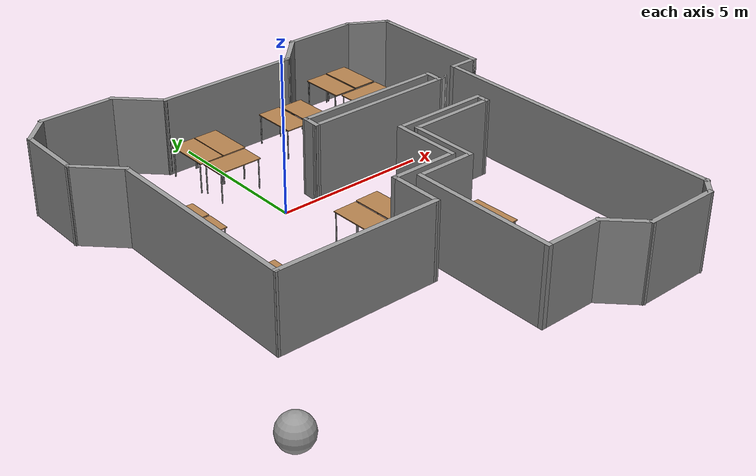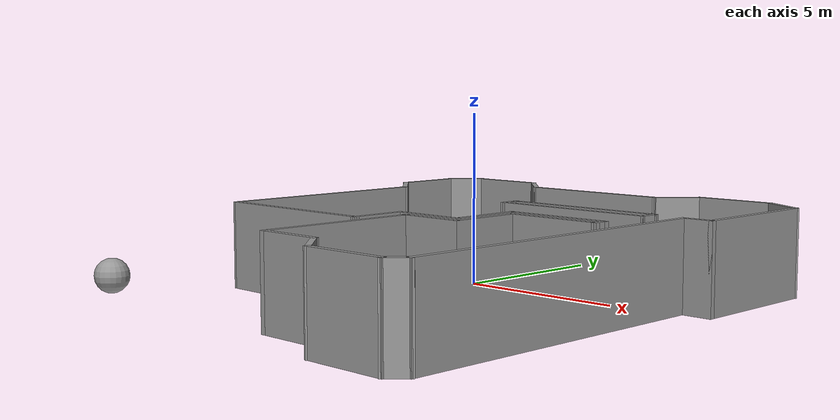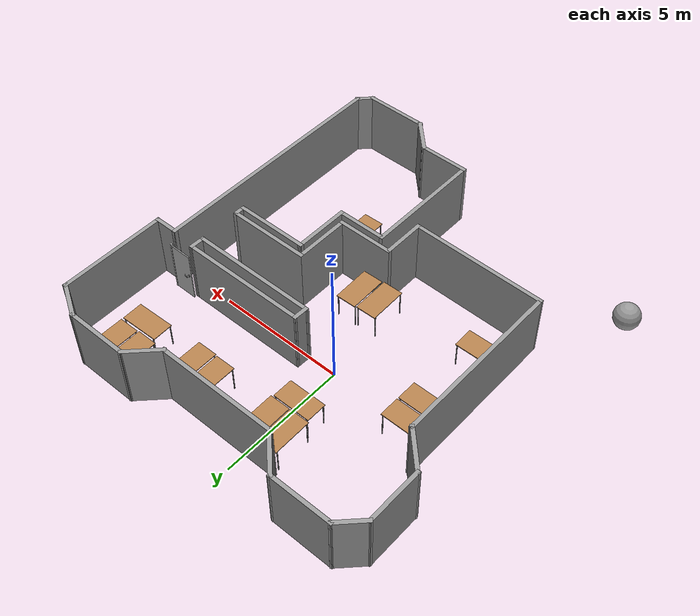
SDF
<?xml version='1.0'?>
<sdf version='1.6'>
  <model name='office_1_model'>
    <model name='drc_practice_weighted_door'>
      <link name='frame'>
        <pose frame=''>0.06 -0.0005 0 0 -0 0</pose>
        <inertial>
          <pose frame=''>-0.025145 -0.03429 1.0541 0 -0 0</pose>
          <mass>19</mass>
          <inertia>
            <ixx>7.04458</ixx>
            <ixy>0</ixy>
            <ixz>0</ixz>
            <iyy>7.04114</iyy>
            <iyz>0</iyz>
            <izz>0.0114511</izz>
          </inertia>
        </inertial>
        <collision name='collision_2'>
          <pose frame=''>-0.025145 -0.03429 1.0541 0 -0 0</pose>
          <geometry>
            <box>
              <size>0.05029 0.06858 2.1082</size>
            </box>
          </geometry>
        </collision>
        <visual name='visual'>
          <pose frame=''>-0.025145 -0.03429 1.0541 0 -0 0</pose>
          <geometry>
            <box>
              <size>0.05029 0.06858 2.1082</size>
            </box>
          </geometry>
          <material>
            <script>
              <uri>file://media/materials/scripts/gazebo.material</uri>
              <name>Gazebo/White</name>
            </script>
          </material>
        </visual>
      </link>
      <link name='door'>
        <pose frame=''>-0 0 2.04 3.14159 -0 0</pose>
        <inertial>
          <mass>41.3256</mass>
          <pose frame=''>0.4569 0.0349 1.016 0 -0 0</pose>
          <inertia>
            <ixx>14.2263</ixx>
            <ixy>0</ixy>
            <ixz>0</ixz>
            <iyy>17.099</iyy>
            <iyz>0</iyz>
            <izz>2.88626</izz>
          </inertia>
        </inertial>
        <collision name='collision'>
          <pose frame=''>0.4569 0.0349 1.016 0 -0 0</pose>
          <geometry>
            <box>
              <size>0.9144 0.04445 2.032</size>
            </box>
          </geometry>
        </collision>
        <visual name='visual'>
          <pose frame=''>0 -0.06858 0 0 -0 0</pose>
          <geometry>
            <mesh>
              <uri>model://hinged_door/meshes/door.dae</uri>
            </mesh>
          </geometry>
        </visual>
      </link>
      <link name='handles'>
        <pose frame=''>0.8144 -0.07 1.05 0 -0 3.14159</pose>
        <inertial>
          <pose frame=''>0 -0.035 0 0 -0 0</pose>
          <mass>2</mass>
          <inertia>
            <ixx>0.0110115</ixx>
            <ixy>-0</ixy>
            <ixz>-0.00647057</ixz>
            <iyy>0.0190181</iyy>
            <iyz>0</iyz>
            <izz>0.00824372</izz>
          </inertia>
        </inertial>
        <collision name='handle1_collision'>
          <pose frame=''>0.015 -0.015 0 -1.57 0 0</pose>
          <geometry>
            <mesh>
              <uri>model://door_handle/meshes/handle.dae</uri>
            </mesh>
          </geometry>
        </collision>
        <visual name='handle1_visual'>
          <pose frame=''>0.015 -0.015 0 -1.57 0 0</pose>
          <geometry>
            <mesh>
              <uri>model://door_handle/meshes/handle.dae</uri>
            </mesh>
          </geometry>
        </visual>
        <collision name='handle2_collision'>
          <pose frame=''>0.015 -0.055 0 1.57 -0 0</pose>
          <geometry>
            <mesh>
              <uri>model://door_handle/meshes/handle.dae</uri>
            </mesh>
          </geometry>
        </collision>
        <visual name='handle2_visual'>
          <pose frame=''>0.015 -0.055 0 1.57 -0 0</pose>
          <geometry>
            <mesh>
              <uri>model://door_handle/meshes/handle.dae</uri>
            </mesh>
          </geometry>
        </visual>
      </link>
      <joint name='handle' type='revolute'>
        <parent>door</parent>
        <child>handles</child>
        <pose frame=''>0.015 0 0 0 -0 0</pose>
        <axis>
          <xyz>0 1 0</xyz>
          <limit>
            <lower>-1.58</lower>
            <upper>0</upper>
          </limit>
          <dynamics>
            <damping>1</damping>
            <friction>10</friction>
            <spring_reference>0</spring_reference>
            <spring_stiffness>0</spring_stiffness>
          </dynamics>
          <use_parent_model_frame>1</use_parent_model_frame>
          <use_parent_model_frame>1</use_parent_model_frame>
        </axis>
        <physics>
          <ode>
            <cfm_damping>1</cfm_damping>
          </ode>
        </physics>
      </joint>
      <joint name='hinge' type='revolute'>
        <parent>frame</parent>
        <child>door</child>
        <axis>
          <xyz>0 0 1</xyz>
          <limit>
            <lower>-1.58</lower>
            <upper>0</upper>
          </limit>
          <dynamics>
            <damping>15.5365</damping>
            <friction>15.5365</friction>
            <spring_reference>0</spring_reference>
            <spring_stiffness>0</spring_stiffness>
          </dynamics>
          <use_parent_model_frame>1</use_parent_model_frame>
          <use_parent_model_frame>1</use_parent_model_frame>
        </axis>
        <physics>
          <ode>
            <cfm_damping>1</cfm_damping>
          </ode>
        </physics>
      </joint>
      <joint name='world_joint' type='revolute'>
        <child>frame</child>
        <parent>world</parent>
        <axis>
          <limit>
            <lower>0</lower>
            <upper>0</upper>
          </limit>
          <xyz>0 1 0</xyz>
          <dynamics>
            <damping>1</damping>
            <spring_reference>0</spring_reference>
            <spring_stiffness>0</spring_stiffness>
          </dynamics>
          <use_parent_model_frame>1</use_parent_model_frame>
          <use_parent_model_frame>1</use_parent_model_frame>
        </axis>
        <physics>
          <ode>
            <cfm_damping>1</cfm_damping>
          </ode>
        </physics>
      </joint>
      <pose frame=''>6.98509 0.627583 0 0 -0 3.13261</pose>
    </model>
    <model name='office_1'>
      <link name='Wall_10'>
        <pose frame=''>-2.97115 6.92234 0 0 0 -0.785398</pose>
        <self_collide>0</self_collide>
        <enable_wind>0</enable_wind>
        <kinematic>0</kinematic>
        <visual name='Wall_10_Visual'>
          <pose frame=''>0 0 1.25 0 -0 0</pose>
          <geometry>
            <box>
              <size>1.75 0.15 2.5</size>
            </box>
          </geometry>
          <material>
            <script>
              <uri>file://media/materials/scripts/gazebo.material</uri>
              <name>Gazebo/Grey</name>
            </script>
            <ambient>1 1 1 1</ambient>
            <shader type='pixel'/>
          </material>
          <meta>
            <layer>0</layer>
          </meta>
          <transparency>0</transparency>
          <cast_shadows>1</cast_shadows>
        </visual>
        <collision name='Wall_10_Collision'>
          <laser_retro>0</laser_retro>
          <max_contacts>10</max_contacts>
          <pose frame=''>0 0 1.25 0 -0 0</pose>
          <geometry>
            <box>
              <size>1.75 0.15 2.5</size>
            </box>
          </geometry>
          <surface>
            <friction>
              <ode>
                <mu>1</mu>
                <mu2>1</mu2>
                <fdir1>0 0 0</fdir1>
                <slip1>0</slip1>
                <slip2>0</slip2>
              </ode>
              <torsional>
                <coefficient>1</coefficient>
                <patch_radius>0</patch_radius>
                <surface_radius>0</surface_radius>
                <use_patch_radius>1</use_patch_radius>
                <ode>
                  <slip>0</slip>
                </ode>
              </torsional>
            </friction>
            <bounce>
              <restitution_coefficient>0</restitution_coefficient>
              <threshold>1e+06</threshold>
            </bounce>
            <contact>
              <collide_without_contact>0</collide_without_contact>
              <collide_without_contact_bitmask>1</collide_without_contact_bitmask>
              <collide_bitmask>1</collide_bitmask>
              <ode>
                <soft_cfm>0</soft_cfm>
                <soft_erp>0.2</soft_erp>
                <kp>1e+13</kp>
                <kd>1</kd>
                <max_vel>0.01</max_vel>
                <min_depth>0</min_depth>
              </ode>
              <bullet>
                <split_impulse>1</split_impulse>
                <split_impulse_penetration_threshold>-0.01</split_impulse_penetration_threshold>
                <soft_cfm>0</soft_cfm>
                <soft_erp>0.2</soft_erp>
                <kp>1e+13</kp>
                <kd>1</kd>
              </bullet>
            </contact>
          </surface>
        </collision>
      </link>
      <link name='Wall_11'>
        <pose frame=''>-0.105463 6.35665 0 0 -0 0</pose>
        <self_collide>0</self_collide>
        <enable_wind>0</enable_wind>
        <kinematic>0</kinematic>
        <visual name='Wall_11_Visual'>
          <pose frame=''>0 0 1.25 0 -0 0</pose>
          <geometry>
            <box>
              <size>4.75 0.15 2.5</size>
            </box>
          </geometry>
          <material>
            <script>
              <uri>file://media/materials/scripts/gazebo.material</uri>
              <name>Gazebo/Grey</name>
            </script>
            <ambient>1 1 1 1</ambient>
            <shader type='pixel'/>
          </material>
          <meta>
            <layer>0</layer>
          </meta>
          <transparency>0</transparency>
          <cast_shadows>1</cast_shadows>
        </visual>
        <collision name='Wall_11_Collision'>
          <laser_retro>0</laser_retro>
          <max_contacts>10</max_contacts>
          <pose frame=''>0 0 1.25 0 -0 0</pose>
          <geometry>
            <box>
              <size>4.75 0.15 2.5</size>
            </box>
          </geometry>
          <surface>
            <friction>
              <ode>
                <mu>1</mu>
                <mu2>1</mu2>
                <fdir1>0 0 0</fdir1>
                <slip1>0</slip1>
                <slip2>0</slip2>
              </ode>
              <torsional>
                <coefficient>1</coefficient>
                <patch_radius>0</patch_radius>
                <surface_radius>0</surface_radius>
                <use_patch_radius>1</use_patch_radius>
                <ode>
                  <slip>0</slip>
                </ode>
              </torsional>
            </friction>
            <bounce>
              <restitution_coefficient>0</restitution_coefficient>
              <threshold>1e+06</threshold>
            </bounce>
            <contact>
              <collide_without_contact>0</collide_without_contact>
              <collide_without_contact_bitmask>1</collide_without_contact_bitmask>
              <collide_bitmask>1</collide_bitmask>
              <ode>
                <soft_cfm>0</soft_cfm>
                <soft_erp>0.2</soft_erp>
                <kp>1e+13</kp>
                <kd>1</kd>
                <max_vel>0.01</max_vel>
                <min_depth>0</min_depth>
              </ode>
              <bullet>
                <split_impulse>1</split_impulse>
                <split_impulse_penetration_threshold>-0.01</split_impulse_penetration_threshold>
                <soft_cfm>0</soft_cfm>
                <soft_erp>0.2</soft_erp>
                <kp>1e+13</kp>
                <kd>1</kd>
              </bullet>
            </contact>
          </surface>
        </collision>
      </link>
      <link name='Wall_12'>
        <pose frame=''>2.67183 6.83395 0 0 -0 0.785398</pose>
        <self_collide>0</self_collide>
        <enable_wind>0</enable_wind>
        <kinematic>0</kinematic>
        <visual name='Wall_12_Visual'>
          <pose frame=''>0 0 1.25 0 -0 0</pose>
          <geometry>
            <box>
              <size>1.5 0.15 2.5</size>
            </box>
          </geometry>
          <material>
            <script>
              <uri>file://media/materials/scripts/gazebo.material</uri>
              <name>Gazebo/Grey</name>
            </script>
            <ambient>1 1 1 1</ambient>
            <shader type='pixel'/>
          </material>
          <meta>
            <layer>0</layer>
          </meta>
          <transparency>0</transparency>
          <cast_shadows>1</cast_shadows>
        </visual>
        <collision name='Wall_12_Collision'>
          <laser_retro>0</laser_retro>
          <max_contacts>10</max_contacts>
          <pose frame=''>0 0 1.25 0 -0 0</pose>
          <geometry>
            <box>
              <size>1.5 0.15 2.5</size>
            </box>
          </geometry>
          <surface>
            <friction>
              <ode>
                <mu>1</mu>
                <mu2>1</mu2>
                <fdir1>0 0 0</fdir1>
                <slip1>0</slip1>
                <slip2>0</slip2>
              </ode>
              <torsional>
                <coefficient>1</coefficient>
                <patch_radius>0</patch_radius>
                <surface_radius>0</surface_radius>
                <use_patch_radius>1</use_patch_radius>
                <ode>
                  <slip>0</slip>
                </ode>
              </torsional>
            </friction>
            <bounce>
              <restitution_coefficient>0</restitution_coefficient>
              <threshold>1e+06</threshold>
            </bounce>
            <contact>
              <collide_without_contact>0</collide_without_contact>
              <collide_without_contact_bitmask>1</collide_without_contact_bitmask>
              <collide_bitmask>1</collide_bitmask>
              <ode>
                <soft_cfm>0</soft_cfm>
                <soft_erp>0.2</soft_erp>
                <kp>1e+13</kp>
                <kd>1</kd>
                <max_vel>0.01</max_vel>
                <min_depth>0</min_depth>
              </ode>
              <bullet>
                <split_impulse>1</split_impulse>
                <split_impulse_penetration_threshold>-0.01</split_impulse_penetration_threshold>
                <soft_cfm>0</soft_cfm>
                <soft_erp>0.2</soft_erp>
                <kp>1e+13</kp>
                <kd>1</kd>
              </bullet>
            </contact>
          </surface>
        </collision>
      </link>
      <link name='Wall_13'>
        <pose frame=''>4.32413 7.31124 0 0 -0 0</pose>
        <self_collide>0</self_collide>
        <enable_wind>0</enable_wind>
        <kinematic>0</kinematic>
        <visual name='Wall_13_Visual'>
          <pose frame=''>0 0 1.25 0 -0 0</pose>
          <geometry>
            <box>
              <size>2.5 0.15 2.5</size>
            </box>
          </geometry>
          <material>
            <script>
              <uri>file://media/materials/scripts/gazebo.material</uri>
              <name>Gazebo/Grey</name>
            </script>
            <ambient>1 1 1 1</ambient>
            <shader type='pixel'/>
          </material>
          <meta>
            <layer>0</layer>
          </meta>
          <transparency>0</transparency>
          <cast_shadows>1</cast_shadows>
        </visual>
        <collision name='Wall_13_Collision'>
          <laser_retro>0</laser_retro>
          <max_contacts>10</max_contacts>
          <pose frame=''>0 0 1.25 0 -0 0</pose>
          <geometry>
            <box>
              <size>2.5 0.15 2.5</size>
            </box>
          </geometry>
          <surface>
            <friction>
              <ode>
                <mu>1</mu>
                <mu2>1</mu2>
                <fdir1>0 0 0</fdir1>
                <slip1>0</slip1>
                <slip2>0</slip2>
              </ode>
              <torsional>
                <coefficient>1</coefficient>
                <patch_radius>0</patch_radius>
                <surface_radius>0</surface_radius>
                <use_patch_radius>1</use_patch_radius>
                <ode>
                  <slip>0</slip>
                </ode>
              </torsional>
            </friction>
            <bounce>
              <restitution_coefficient>0</restitution_coefficient>
              <threshold>1e+06</threshold>
            </bounce>
            <contact>
              <collide_without_contact>0</collide_without_contact>
              <collide_without_contact_bitmask>1</collide_without_contact_bitmask>
              <collide_bitmask>1</collide_bitmask>
              <ode>
                <soft_cfm>0</soft_cfm>
                <soft_erp>0.2</soft_erp>
                <kp>1e+13</kp>
                <kd>1</kd>
                <max_vel>0.01</max_vel>
                <min_depth>0</min_depth>
              </ode>
              <bullet>
                <split_impulse>1</split_impulse>
                <split_impulse_penetration_threshold>-0.01</split_impulse_penetration_threshold>
                <soft_cfm>0</soft_cfm>
                <soft_erp>0.2</soft_erp>
                <kp>1e+13</kp>
                <kd>1</kd>
              </bullet>
            </contact>
          </surface>
        </collision>
      </link>
      <link name='Wall_14'>
        <pose frame=''>6.0837 6.97374 0 0 0 -0.523599</pose>
        <self_collide>0</self_collide>
        <enable_wind>0</enable_wind>
        <kinematic>0</kinematic>
        <visual name='Wall_14_Visual'>
          <pose frame=''>0 0 1.25 0 -0 0</pose>
          <geometry>
            <box>
              <size>1.5 0.15 2.5</size>
            </box>
          </geometry>
          <material>
            <script>
              <uri>file://media/materials/scripts/gazebo.material</uri>
              <name>Gazebo/Grey</name>
            </script>
            <ambient>1 1 1 1</ambient>
            <shader type='pixel'/>
          </material>
          <meta>
            <layer>0</layer>
          </meta>
          <transparency>0</transparency>
          <cast_shadows>1</cast_shadows>
        </visual>
        <collision name='Wall_14_Collision'>
          <laser_retro>0</laser_retro>
          <max_contacts>10</max_contacts>
          <pose frame=''>0 0 1.25 0 -0 0</pose>
          <geometry>
            <box>
              <size>1.5 0.15 2.5</size>
            </box>
          </geometry>
          <surface>
            <friction>
              <ode>
                <mu>1</mu>
                <mu2>1</mu2>
                <fdir1>0 0 0</fdir1>
                <slip1>0</slip1>
                <slip2>0</slip2>
              </ode>
              <torsional>
                <coefficient>1</coefficient>
                <patch_radius>0</patch_radius>
                <surface_radius>0</surface_radius>
                <use_patch_radius>1</use_patch_radius>
                <ode>
                  <slip>0</slip>
                </ode>
              </torsional>
            </friction>
            <bounce>
              <restitution_coefficient>0</restitution_coefficient>
              <threshold>1e+06</threshold>
            </bounce>
            <contact>
              <collide_without_contact>0</collide_without_contact>
              <collide_without_contact_bitmask>1</collide_without_contact_bitmask>
              <collide_bitmask>1</collide_bitmask>
              <ode>
                <soft_cfm>0</soft_cfm>
                <soft_erp>0.2</soft_erp>
                <kp>1e+13</kp>
                <kd>1</kd>
                <max_vel>0.01</max_vel>
                <min_depth>0</min_depth>
              </ode>
              <bullet>
                <split_impulse>1</split_impulse>
                <split_impulse_penetration_threshold>-0.01</split_impulse_penetration_threshold>
                <soft_cfm>0</soft_cfm>
                <soft_erp>0.2</soft_erp>
                <kp>1e+13</kp>
                <kd>1</kd>
              </bullet>
            </contact>
          </surface>
        </collision>
      </link>
      <link name='Wall_15'>
        <pose frame=''>6.66826 4.58624 0 0 0 -1.5708</pose>
        <self_collide>0</self_collide>
        <enable_wind>0</enable_wind>
        <kinematic>0</kinematic>
        <visual name='Wall_15_Visual'>
          <pose frame=''>0 0 1.25 0 -0 0</pose>
          <geometry>
            <box>
              <size>4.25 0.15 2.5</size>
            </box>
          </geometry>
          <material>
            <script>
              <uri>file://media/materials/scripts/gazebo.material</uri>
              <name>Gazebo/Grey</name>
            </script>
            <ambient>1 1 1 1</ambient>
            <shader type='pixel'/>
          </material>
          <meta>
            <layer>0</layer>
          </meta>
          <transparency>0</transparency>
          <cast_shadows>1</cast_shadows>
        </visual>
        <collision name='Wall_15_Collision'>
          <laser_retro>0</laser_retro>
          <max_contacts>10</max_contacts>
          <pose frame=''>0 0 1.25 0 -0 0</pose>
          <geometry>
            <box>
              <size>4.25 0.15 2.5</size>
            </box>
          </geometry>
          <surface>
            <friction>
              <ode>
                <mu>1</mu>
                <mu2>1</mu2>
                <fdir1>0 0 0</fdir1>
                <slip1>0</slip1>
                <slip2>0</slip2>
              </ode>
              <torsional>
                <coefficient>1</coefficient>
                <patch_radius>0</patch_radius>
                <surface_radius>0</surface_radius>
                <use_patch_radius>1</use_patch_radius>
                <ode>
                  <slip>0</slip>
                </ode>
              </torsional>
            </friction>
            <bounce>
              <restitution_coefficient>0</restitution_coefficient>
              <threshold>1e+06</threshold>
            </bounce>
            <contact>
              <collide_without_contact>0</collide_without_contact>
              <collide_without_contact_bitmask>1</collide_without_contact_bitmask>
              <collide_bitmask>1</collide_bitmask>
              <ode>
                <soft_cfm>0</soft_cfm>
                <soft_erp>0.2</soft_erp>
                <kp>1e+13</kp>
                <kd>1</kd>
                <max_vel>0.01</max_vel>
                <min_depth>0</min_depth>
              </ode>
              <bullet>
                <split_impulse>1</split_impulse>
                <split_impulse_penetration_threshold>-0.01</split_impulse_penetration_threshold>
                <soft_cfm>0</soft_cfm>
                <soft_erp>0.2</soft_erp>
                <kp>1e+13</kp>
                <kd>1</kd>
              </bullet>
            </contact>
          </surface>
        </collision>
      </link>
      <link name='Wall_16'>
        <pose frame=''>6.24327 2.53624 0 0 -0 3.14159</pose>
        <self_collide>0</self_collide>
        <enable_wind>0</enable_wind>
        <kinematic>0</kinematic>
        <visual name='Wall_16_Visual'>
          <pose frame=''>0 0 1.25 0 -0 0</pose>
          <geometry>
            <box>
              <size>1 0.15 2.5</size>
            </box>
          </geometry>
          <material>
            <script>
              <uri>file://media/materials/scripts/gazebo.material</uri>
              <name>Gazebo/Grey</name>
            </script>
            <ambient>1 1 1 1</ambient>
            <shader type='pixel'/>
          </material>
          <meta>
            <layer>0</layer>
          </meta>
          <transparency>0</transparency>
          <cast_shadows>1</cast_shadows>
        </visual>
        <collision name='Wall_16_Collision'>
          <laser_retro>0</laser_retro>
          <max_contacts>10</max_contacts>
          <pose frame=''>0 0 1.25 0 -0 0</pose>
          <geometry>
            <box>
              <size>1 0.15 2.5</size>
            </box>
          </geometry>
          <surface>
            <friction>
              <ode>
                <mu>1</mu>
                <mu2>1</mu2>
                <fdir1>0 0 0</fdir1>
                <slip1>0</slip1>
                <slip2>0</slip2>
              </ode>
              <torsional>
                <coefficient>1</coefficient>
                <patch_radius>0</patch_radius>
                <surface_radius>0</surface_radius>
                <use_patch_radius>1</use_patch_radius>
                <ode>
                  <slip>0</slip>
                </ode>
              </torsional>
            </friction>
            <bounce>
              <restitution_coefficient>0</restitution_coefficient>
              <threshold>1e+06</threshold>
            </bounce>
            <contact>
              <collide_without_contact>0</collide_without_contact>
              <collide_without_contact_bitmask>1</collide_without_contact_bitmask>
              <collide_bitmask>1</collide_bitmask>
              <ode>
                <soft_cfm>0</soft_cfm>
                <soft_erp>0.2</soft_erp>
                <kp>1e+13</kp>
                <kd>1</kd>
                <max_vel>0.01</max_vel>
                <min_depth>0</min_depth>
              </ode>
              <bullet>
                <split_impulse>1</split_impulse>
                <split_impulse_penetration_threshold>-0.01</split_impulse_penetration_threshold>
                <soft_cfm>0</soft_cfm>
                <soft_erp>0.2</soft_erp>
                <kp>1e+13</kp>
                <kd>1</kd>
              </bullet>
            </contact>
          </surface>
        </collision>
      </link>
      <link name='Wall_17'>
        <pose frame=''>5.81827 -2.26376 0 0 0 -1.5708</pose>
        <self_collide>0</self_collide>
        <enable_wind>0</enable_wind>
        <kinematic>0</kinematic>
        <visual name='Wall_17_Visual'>
          <pose frame=''>0 0 1.25 0 -0 0</pose>
          <geometry>
            <box>
              <size>9.75 0.15 2.5</size>
            </box>
          </geometry>
          <material>
            <script>
              <uri>file://media/materials/scripts/gazebo.material</uri>
              <name>Gazebo/Grey</name>
            </script>
            <ambient>1 1 1 1</ambient>
            <shader type='pixel'/>
          </material>
          <meta>
            <layer>0</layer>
          </meta>
          <transparency>0</transparency>
          <cast_shadows>1</cast_shadows>
        </visual>
        <collision name='Wall_17_Collision'>
          <laser_retro>0</laser_retro>
          <max_contacts>10</max_contacts>
          <pose frame=''>0 0 1.25 0 -0 0</pose>
          <geometry>
            <box>
              <size>9.75 0.15 2.5</size>
            </box>
          </geometry>
          <surface>
            <friction>
              <ode>
                <mu>1</mu>
                <mu2>1</mu2>
                <fdir1>0 0 0</fdir1>
                <slip1>0</slip1>
                <slip2>0</slip2>
              </ode>
              <torsional>
                <coefficient>1</coefficient>
                <patch_radius>0</patch_radius>
                <surface_radius>0</surface_radius>
                <use_patch_radius>1</use_patch_radius>
                <ode>
                  <slip>0</slip>
                </ode>
              </torsional>
            </friction>
            <bounce>
              <restitution_coefficient>0</restitution_coefficient>
              <threshold>1e+06</threshold>
            </bounce>
            <contact>
              <collide_without_contact>0</collide_without_contact>
              <collide_without_contact_bitmask>1</collide_without_contact_bitmask>
              <collide_bitmask>1</collide_bitmask>
              <ode>
                <soft_cfm>0</soft_cfm>
                <soft_erp>0.2</soft_erp>
                <kp>1e+13</kp>
                <kd>1</kd>
                <max_vel>0.01</max_vel>
                <min_depth>0</min_depth>
              </ode>
              <bullet>
                <split_impulse>1</split_impulse>
                <split_impulse_penetration_threshold>-0.01</split_impulse_penetration_threshold>
                <soft_cfm>0</soft_cfm>
                <soft_erp>0.2</soft_erp>
                <kp>1e+13</kp>
                <kd>1</kd>
              </bullet>
            </contact>
          </surface>
        </collision>
      </link>
      <link name='Wall_18'>
        <pose frame=''>5.60613 -7.27589 0 0 0 -2.35619</pose>
        <self_collide>0</self_collide>
        <enable_wind>0</enable_wind>
        <kinematic>0</kinematic>
        <visual name='Wall_18_Visual'>
          <pose frame=''>0 0 1.25 0 -0 0</pose>
          <geometry>
            <box>
              <size>0.75 0.15 2.5</size>
            </box>
          </geometry>
          <material>
            <script>
              <uri>file://media/materials/scripts/gazebo.material</uri>
              <name>Gazebo/Grey</name>
            </script>
            <ambient>1 1 1 1</ambient>
            <shader type='pixel'/>
          </material>
          <meta>
            <layer>0</layer>
          </meta>
          <transparency>0</transparency>
          <cast_shadows>1</cast_shadows>
        </visual>
        <collision name='Wall_18_Collision'>
          <laser_retro>0</laser_retro>
          <max_contacts>10</max_contacts>
          <pose frame=''>0 0 1.25 0 -0 0</pose>
          <geometry>
            <box>
              <size>0.75 0.15 2.5</size>
            </box>
          </geometry>
          <surface>
            <friction>
              <ode>
                <mu>1</mu>
                <mu2>1</mu2>
                <fdir1>0 0 0</fdir1>
                <slip1>0</slip1>
                <slip2>0</slip2>
              </ode>
              <torsional>
                <coefficient>1</coefficient>
                <patch_radius>0</patch_radius>
                <surface_radius>0</surface_radius>
                <use_patch_radius>1</use_patch_radius>
                <ode>
                  <slip>0</slip>
                </ode>
              </torsional>
            </friction>
            <bounce>
              <restitution_coefficient>0</restitution_coefficient>
              <threshold>1e+06</threshold>
            </bounce>
            <contact>
              <collide_without_contact>0</collide_without_contact>
              <collide_without_contact_bitmask>1</collide_without_contact_bitmask>
              <collide_bitmask>1</collide_bitmask>
              <ode>
                <soft_cfm>0</soft_cfm>
                <soft_erp>0.2</soft_erp>
                <kp>1e+13</kp>
                <kd>1</kd>
                <max_vel>0.01</max_vel>
                <min_depth>0</min_depth>
              </ode>
              <bullet>
                <split_impulse>1</split_impulse>
                <split_impulse_penetration_threshold>-0.01</split_impulse_penetration_threshold>
                <soft_cfm>0</soft_cfm>
                <soft_erp>0.2</soft_erp>
                <kp>1e+13</kp>
                <kd>1</kd>
              </bullet>
            </contact>
          </surface>
        </collision>
      </link>
      <link name='Wall_19'>
        <pose frame=''>4.219 -7.48802 0 0 -0 3.14159</pose>
        <self_collide>0</self_collide>
        <enable_wind>0</enable_wind>
        <kinematic>0</kinematic>
        <visual name='Wall_19_Visual'>
          <pose frame=''>0 0 1.25 0 -0 0</pose>
          <geometry>
            <box>
              <size>2.5 0.15 2.5</size>
            </box>
          </geometry>
          <material>
            <script>
              <uri>file://media/materials/scripts/gazebo.material</uri>
              <name>Gazebo/Grey</name>
            </script>
            <ambient>1 1 1 1</ambient>
            <shader type='pixel'/>
          </material>
          <meta>
            <layer>0</layer>
          </meta>
          <transparency>0</transparency>
          <cast_shadows>1</cast_shadows>
        </visual>
        <collision name='Wall_19_Collision'>
          <laser_retro>0</laser_retro>
          <max_contacts>10</max_contacts>
          <pose frame=''>0 0 1.25 0 -0 0</pose>
          <geometry>
            <box>
              <size>2.5 0.15 2.5</size>
            </box>
          </geometry>
          <surface>
            <friction>
              <ode>
                <mu>1</mu>
                <mu2>1</mu2>
                <fdir1>0 0 0</fdir1>
                <slip1>0</slip1>
                <slip2>0</slip2>
              </ode>
              <torsional>
                <coefficient>1</coefficient>
                <patch_radius>0</patch_radius>
                <surface_radius>0</surface_radius>
                <use_patch_radius>1</use_patch_radius>
                <ode>
                  <slip>0</slip>
                </ode>
              </torsional>
            </friction>
            <bounce>
              <restitution_coefficient>0</restitution_coefficient>
              <threshold>1e+06</threshold>
            </bounce>
            <contact>
              <collide_without_contact>0</collide_without_contact>
              <collide_without_contact_bitmask>1</collide_without_contact_bitmask>
              <collide_bitmask>1</collide_bitmask>
              <ode>
                <soft_cfm>0</soft_cfm>
                <soft_erp>0.2</soft_erp>
                <kp>1e+13</kp>
                <kd>1</kd>
                <max_vel>0.01</max_vel>
                <min_depth>0</min_depth>
              </ode>
              <bullet>
                <split_impulse>1</split_impulse>
                <split_impulse_penetration_threshold>-0.01</split_impulse_penetration_threshold>
                <soft_cfm>0</soft_cfm>
                <soft_erp>0.2</soft_erp>
                <kp>1e+13</kp>
                <kd>1</kd>
              </bullet>
            </contact>
          </surface>
        </collision>
      </link>
      <link name='Wall_20'>
        <pose frame=''>2.5667 -7.01072 0 0 -0 2.35619</pose>
        <self_collide>0</self_collide>
        <enable_wind>0</enable_wind>
        <kinematic>0</kinematic>
        <visual name='Wall_20_Visual'>
          <pose frame=''>0 0 1.25 0 -0 0</pose>
          <geometry>
            <box>
              <size>1.5 0.15 2.5</size>
            </box>
          </geometry>
          <material>
            <script>
              <uri>file://media/materials/scripts/gazebo.material</uri>
              <name>Gazebo/Grey</name>
            </script>
            <ambient>1 1 1 1</ambient>
            <shader type='pixel'/>
          </material>
          <meta>
            <layer>0</layer>
          </meta>
          <transparency>0</transparency>
          <cast_shadows>1</cast_shadows>
        </visual>
        <collision name='Wall_20_Collision'>
          <laser_retro>0</laser_retro>
          <max_contacts>10</max_contacts>
          <pose frame=''>0 0 1.25 0 -0 0</pose>
          <geometry>
            <box>
              <size>1.5 0.15 2.5</size>
            </box>
          </geometry>
          <surface>
            <friction>
              <ode>
                <mu>1</mu>
                <mu2>1</mu2>
                <fdir1>0 0 0</fdir1>
                <slip1>0</slip1>
                <slip2>0</slip2>
              </ode>
              <torsional>
                <coefficient>1</coefficient>
                <patch_radius>0</patch_radius>
                <surface_radius>0</surface_radius>
                <use_patch_radius>1</use_patch_radius>
                <ode>
                  <slip>0</slip>
                </ode>
              </torsional>
            </friction>
            <bounce>
              <restitution_coefficient>0</restitution_coefficient>
              <threshold>1e+06</threshold>
            </bounce>
            <contact>
              <collide_without_contact>0</collide_without_contact>
              <collide_without_contact_bitmask>1</collide_without_contact_bitmask>
              <collide_bitmask>1</collide_bitmask>
              <ode>
                <soft_cfm>0</soft_cfm>
                <soft_erp>0.2</soft_erp>
                <kp>1e+13</kp>
                <kd>1</kd>
                <max_vel>0.01</max_vel>
                <min_depth>0</min_depth>
              </ode>
              <bullet>
                <split_impulse>1</split_impulse>
                <split_impulse_penetration_threshold>-0.01</split_impulse_penetration_threshold>
                <soft_cfm>0</soft_cfm>
                <soft_erp>0.2</soft_erp>
                <kp>1e+13</kp>
                <kd>1</kd>
              </bullet>
            </contact>
          </surface>
        </collision>
      </link>
      <link name='Wall_21'>
        <pose frame=''>1.16441 -6.53343 0 0 -0 3.14159</pose>
        <self_collide>0</self_collide>
        <enable_wind>0</enable_wind>
        <kinematic>0</kinematic>
        <visual name='Wall_21_Visual'>
          <pose frame=''>0 0 1.25 0 -0 0</pose>
          <geometry>
            <box>
              <size>2 0.15 2.5</size>
            </box>
          </geometry>
          <material>
            <script>
              <uri>file://media/materials/scripts/gazebo.material</uri>
              <name>Gazebo/Grey</name>
            </script>
            <ambient>1 1 1 1</ambient>
            <shader type='pixel'/>
          </material>
          <meta>
            <layer>0</layer>
          </meta>
          <transparency>0</transparency>
          <cast_shadows>1</cast_shadows>
        </visual>
        <collision name='Wall_21_Collision'>
          <laser_retro>0</laser_retro>
          <max_contacts>10</max_contacts>
          <pose frame=''>0 0 1.25 0 -0 0</pose>
          <geometry>
            <box>
              <size>2 0.15 2.5</size>
            </box>
          </geometry>
          <surface>
            <friction>
              <ode>
                <mu>1</mu>
                <mu2>1</mu2>
                <fdir1>0 0 0</fdir1>
                <slip1>0</slip1>
                <slip2>0</slip2>
              </ode>
              <torsional>
                <coefficient>1</coefficient>
                <patch_radius>0</patch_radius>
                <surface_radius>0</surface_radius>
                <use_patch_radius>1</use_patch_radius>
                <ode>
                  <slip>0</slip>
                </ode>
              </torsional>
            </friction>
            <bounce>
              <restitution_coefficient>0</restitution_coefficient>
              <threshold>1e+06</threshold>
            </bounce>
            <contact>
              <collide_without_contact>0</collide_without_contact>
              <collide_without_contact_bitmask>1</collide_without_contact_bitmask>
              <collide_bitmask>1</collide_bitmask>
              <ode>
                <soft_cfm>0</soft_cfm>
                <soft_erp>0.2</soft_erp>
                <kp>1e+13</kp>
                <kd>1</kd>
                <max_vel>0.01</max_vel>
                <min_depth>0</min_depth>
              </ode>
              <bullet>
                <split_impulse>1</split_impulse>
                <split_impulse_penetration_threshold>-0.01</split_impulse_penetration_threshold>
                <soft_cfm>0</soft_cfm>
                <soft_erp>0.2</soft_erp>
                <kp>1e+13</kp>
                <kd>1</kd>
              </bullet>
            </contact>
          </surface>
        </collision>
      </link>
      <link name='Wall_22'>
        <pose frame=''>0.239407 -4.23343 0 0 -0 1.5708</pose>
        <self_collide>0</self_collide>
        <enable_wind>0</enable_wind>
        <kinematic>0</kinematic>
        <visual name='Wall_22_Visual'>
          <pose frame=''>0 0 1.25 0 -0 0</pose>
          <geometry>
            <box>
              <size>4.75 0.15 2.5</size>
            </box>
          </geometry>
          <material>
            <script>
              <uri>file://media/materials/scripts/gazebo.material</uri>
              <name>Gazebo/Grey</name>
            </script>
            <ambient>1 1 1 1</ambient>
            <shader type='pixel'/>
          </material>
          <meta>
            <layer>0</layer>
          </meta>
          <transparency>0</transparency>
          <cast_shadows>1</cast_shadows>
        </visual>
        <collision name='Wall_22_Collision'>
          <laser_retro>0</laser_retro>
          <max_contacts>10</max_contacts>
          <pose frame=''>0 0 1.25 0 -0 0</pose>
          <geometry>
            <box>
              <size>4.75 0.15 2.5</size>
            </box>
          </geometry>
          <surface>
            <friction>
              <ode>
                <mu>1</mu>
                <mu2>1</mu2>
                <fdir1>0 0 0</fdir1>
                <slip1>0</slip1>
                <slip2>0</slip2>
              </ode>
              <torsional>
                <coefficient>1</coefficient>
                <patch_radius>0</patch_radius>
                <surface_radius>0</surface_radius>
                <use_patch_radius>1</use_patch_radius>
                <ode>
                  <slip>0</slip>
                </ode>
              </torsional>
            </friction>
            <bounce>
              <restitution_coefficient>0</restitution_coefficient>
              <threshold>1e+06</threshold>
            </bounce>
            <contact>
              <collide_without_contact>0</collide_without_contact>
              <collide_without_contact_bitmask>1</collide_without_contact_bitmask>
              <collide_bitmask>1</collide_bitmask>
              <ode>
                <soft_cfm>0</soft_cfm>
                <soft_erp>0.2</soft_erp>
                <kp>1e+13</kp>
                <kd>1</kd>
                <max_vel>0.01</max_vel>
                <min_depth>0</min_depth>
              </ode>
              <bullet>
                <split_impulse>1</split_impulse>
                <split_impulse_penetration_threshold>-0.01</split_impulse_penetration_threshold>
                <soft_cfm>0</soft_cfm>
                <soft_erp>0.2</soft_erp>
                <kp>1e+13</kp>
                <kd>1</kd>
              </bullet>
            </contact>
          </surface>
        </collision>
      </link>
      <link name='Wall_23'>
        <pose frame=''>1.16441 -1.93343 0 0 -0 0</pose>
        <self_collide>0</self_collide>
        <enable_wind>0</enable_wind>
        <kinematic>0</kinematic>
        <visual name='Wall_23_Visual'>
          <pose frame=''>0 0 1.25 0 -0 0</pose>
          <geometry>
            <box>
              <size>2 0.15 2.5</size>
            </box>
          </geometry>
          <material>
            <script>
              <uri>file://media/materials/scripts/gazebo.material</uri>
              <name>Gazebo/Grey</name>
            </script>
            <ambient>1 1 1 1</ambient>
            <shader type='pixel'/>
          </material>
          <meta>
            <layer>0</layer>
          </meta>
          <transparency>0</transparency>
          <cast_shadows>1</cast_shadows>
        </visual>
        <collision name='Wall_23_Collision'>
          <laser_retro>0</laser_retro>
          <max_contacts>10</max_contacts>
          <pose frame=''>0 0 1.25 0 -0 0</pose>
          <geometry>
            <box>
              <size>2 0.15 2.5</size>
            </box>
          </geometry>
          <surface>
            <friction>
              <ode>
                <mu>1</mu>
                <mu2>1</mu2>
                <fdir1>0 0 0</fdir1>
                <slip1>0</slip1>
                <slip2>0</slip2>
              </ode>
              <torsional>
                <coefficient>1</coefficient>
                <patch_radius>0</patch_radius>
                <surface_radius>0</surface_radius>
                <use_patch_radius>1</use_patch_radius>
                <ode>
                  <slip>0</slip>
                </ode>
              </torsional>
            </friction>
            <bounce>
              <restitution_coefficient>0</restitution_coefficient>
              <threshold>1e+06</threshold>
            </bounce>
            <contact>
              <collide_without_contact>0</collide_without_contact>
              <collide_without_contact_bitmask>1</collide_without_contact_bitmask>
              <collide_bitmask>1</collide_bitmask>
              <ode>
                <soft_cfm>0</soft_cfm>
                <soft_erp>0.2</soft_erp>
                <kp>1e+13</kp>
                <kd>1</kd>
                <max_vel>0.01</max_vel>
                <min_depth>0</min_depth>
              </ode>
              <bullet>
                <split_impulse>1</split_impulse>
                <split_impulse_penetration_threshold>-0.01</split_impulse_penetration_threshold>
                <soft_cfm>0</soft_cfm>
                <soft_erp>0.2</soft_erp>
                <kp>1e+13</kp>
                <kd>1</kd>
              </bullet>
            </contact>
          </surface>
        </collision>
      </link>
      <link name='Wall_24'>
        <pose frame=''>2.08941 -0.883426 0 0 -0 1.5708</pose>
        <self_collide>0</self_collide>
        <enable_wind>0</enable_wind>
        <kinematic>0</kinematic>
        <visual name='Wall_24_Visual'>
          <pose frame=''>0 0 1.25 0 -0 0</pose>
          <geometry>
            <box>
              <size>2.25 0.15 2.5</size>
            </box>
          </geometry>
          <material>
            <script>
              <uri>file://media/materials/scripts/gazebo.material</uri>
              <name>Gazebo/Grey</name>
            </script>
            <ambient>1 1 1 1</ambient>
            <shader type='pixel'/>
          </material>
          <meta>
            <layer>0</layer>
          </meta>
          <transparency>0</transparency>
          <cast_shadows>1</cast_shadows>
        </visual>
        <collision name='Wall_24_Collision'>
          <laser_retro>0</laser_retro>
          <max_contacts>10</max_contacts>
          <pose frame=''>0 0 1.25 0 -0 0</pose>
          <geometry>
            <box>
              <size>2.25 0.15 2.5</size>
            </box>
          </geometry>
          <surface>
            <friction>
              <ode>
                <mu>1</mu>
                <mu2>1</mu2>
                <fdir1>0 0 0</fdir1>
                <slip1>0</slip1>
                <slip2>0</slip2>
              </ode>
              <torsional>
                <coefficient>1</coefficient>
                <patch_radius>0</patch_radius>
                <surface_radius>0</surface_radius>
                <use_patch_radius>1</use_patch_radius>
                <ode>
                  <slip>0</slip>
                </ode>
              </torsional>
            </friction>
            <bounce>
              <restitution_coefficient>0</restitution_coefficient>
              <threshold>1e+06</threshold>
            </bounce>
            <contact>
              <collide_without_contact>0</collide_without_contact>
              <collide_without_contact_bitmask>1</collide_without_contact_bitmask>
              <collide_bitmask>1</collide_bitmask>
              <ode>
                <soft_cfm>0</soft_cfm>
                <soft_erp>0.2</soft_erp>
                <kp>1e+13</kp>
                <kd>1</kd>
                <max_vel>0.01</max_vel>
                <min_depth>0</min_depth>
              </ode>
              <bullet>
                <split_impulse>1</split_impulse>
                <split_impulse_penetration_threshold>-0.01</split_impulse_penetration_threshold>
                <soft_cfm>0</soft_cfm>
                <soft_erp>0.2</soft_erp>
                <kp>1e+13</kp>
                <kd>1</kd>
              </bullet>
            </contact>
          </surface>
        </collision>
      </link>
      <link name='Wall_25'>
        <pose frame=''>3.46784 0.166166 0 0 0 -0.000296</pose>
        <self_collide>0</self_collide>
        <enable_wind>0</enable_wind>
        <kinematic>0</kinematic>
        <visual name='Wall_25_Visual'>
          <pose frame=''>0 0 1.25 0 -0 0</pose>
          <geometry>
            <box>
              <size>2.9069 0.15 2.5</size>
            </box>
          </geometry>
          <material>
            <script>
              <uri>file://media/materials/scripts/gazebo.material</uri>
              <name>Gazebo/Grey</name>
            </script>
            <ambient>1 1 1 1</ambient>
            <shader type='pixel'/>
          </material>
          <meta>
            <layer>0</layer>
          </meta>
          <transparency>0</transparency>
          <cast_shadows>1</cast_shadows>
        </visual>
        <collision name='Wall_25_Collision'>
          <laser_retro>0</laser_retro>
          <max_contacts>10</max_contacts>
          <pose frame=''>0 0 1.25 0 -0 0</pose>
          <geometry>
            <box>
              <size>2.9069 0.15 2.5</size>
            </box>
          </geometry>
          <surface>
            <friction>
              <ode>
                <mu>1</mu>
                <mu2>1</mu2>
                <fdir1>0 0 0</fdir1>
                <slip1>0</slip1>
                <slip2>0</slip2>
              </ode>
              <torsional>
                <coefficient>1</coefficient>
                <patch_radius>0</patch_radius>
                <surface_radius>0</surface_radius>
                <use_patch_radius>1</use_patch_radius>
                <ode>
                  <slip>0</slip>
                </ode>
              </torsional>
            </friction>
            <bounce>
              <restitution_coefficient>0</restitution_coefficient>
              <threshold>1e+06</threshold>
            </bounce>
            <contact>
              <collide_without_contact>0</collide_without_contact>
              <collide_without_contact_bitmask>1</collide_without_contact_bitmask>
              <collide_bitmask>1</collide_bitmask>
              <ode>
                <soft_cfm>0</soft_cfm>
                <soft_erp>0.2</soft_erp>
                <kp>1e+13</kp>
                <kd>1</kd>
                <max_vel>0.01</max_vel>
                <min_depth>0</min_depth>
              </ode>
              <bullet>
                <split_impulse>1</split_impulse>
                <split_impulse_penetration_threshold>-0.01</split_impulse_penetration_threshold>
                <soft_cfm>0</soft_cfm>
                <soft_erp>0.2</soft_erp>
                <kp>1e+13</kp>
                <kd>1</kd>
              </bullet>
            </contact>
          </surface>
        </collision>
      </link>
      <link name='Wall_26'>
        <pose frame=''>4.84626 0.340759 0 0 -0 1.5708</pose>
        <self_collide>0</self_collide>
        <enable_wind>0</enable_wind>
        <kinematic>0</kinematic>
        <visual name='Wall_26_Visual'>
          <pose frame=''>0 0 1.25 0 -0 0</pose>
          <geometry>
            <box>
              <size>0.5 0.15 2.5</size>
            </box>
          </geometry>
          <material>
            <script>
              <uri>file://media/materials/scripts/gazebo.material</uri>
              <name>Gazebo/Grey</name>
            </script>
            <ambient>1 1 1 1</ambient>
            <shader type='pixel'/>
          </material>
          <meta>
            <layer>0</layer>
          </meta>
          <transparency>0</transparency>
          <cast_shadows>1</cast_shadows>
        </visual>
        <collision name='Wall_26_Collision'>
          <laser_retro>0</laser_retro>
          <max_contacts>10</max_contacts>
          <pose frame=''>0 0 1.25 0 -0 0</pose>
          <geometry>
            <box>
              <size>0.5 0.15 2.5</size>
            </box>
          </geometry>
          <surface>
            <friction>
              <ode>
                <mu>1</mu>
                <mu2>1</mu2>
                <fdir1>0 0 0</fdir1>
                <slip1>0</slip1>
                <slip2>0</slip2>
              </ode>
              <torsional>
                <coefficient>1</coefficient>
                <patch_radius>0</patch_radius>
                <surface_radius>0</surface_radius>
                <use_patch_radius>1</use_patch_radius>
                <ode>
                  <slip>0</slip>
                </ode>
              </torsional>
            </friction>
            <bounce>
              <restitution_coefficient>0</restitution_coefficient>
              <threshold>1e+06</threshold>
            </bounce>
            <contact>
              <collide_without_contact>0</collide_without_contact>
              <collide_without_contact_bitmask>1</collide_without_contact_bitmask>
              <collide_bitmask>1</collide_bitmask>
              <ode>
                <soft_cfm>0</soft_cfm>
                <soft_erp>0.2</soft_erp>
                <kp>1e+13</kp>
                <kd>1</kd>
                <max_vel>0.01</max_vel>
                <min_depth>0</min_depth>
              </ode>
              <bullet>
                <split_impulse>1</split_impulse>
                <split_impulse_penetration_threshold>-0.01</split_impulse_penetration_threshold>
                <soft_cfm>0</soft_cfm>
                <soft_erp>0.2</soft_erp>
                <kp>1e+13</kp>
                <kd>1</kd>
              </bullet>
            </contact>
          </surface>
        </collision>
      </link>
      <link name='Wall_27'>
        <pose frame=''>3.29627 0.515759 0 0 -0 3.14159</pose>
        <self_collide>0</self_collide>
        <enable_wind>0</enable_wind>
        <kinematic>0</kinematic>
        <visual name='Wall_27_Visual'>
          <pose frame=''>0 0 1.25 0 -0 0</pose>
          <geometry>
            <box>
              <size>3.25 0.15 2.5</size>
            </box>
          </geometry>
          <material>
            <script>
              <uri>file://media/materials/scripts/gazebo.material</uri>
              <name>Gazebo/Grey</name>
            </script>
            <ambient>1 1 1 1</ambient>
            <shader type='pixel'/>
          </material>
          <meta>
            <layer>0</layer>
          </meta>
          <transparency>0</transparency>
          <cast_shadows>1</cast_shadows>
        </visual>
        <collision name='Wall_27_Collision'>
          <laser_retro>0</laser_retro>
          <max_contacts>10</max_contacts>
          <pose frame=''>0 0 1.25 0 -0 0</pose>
          <geometry>
            <box>
              <size>3.25 0.15 2.5</size>
            </box>
          </geometry>
          <surface>
            <friction>
              <ode>
                <mu>1</mu>
                <mu2>1</mu2>
                <fdir1>0 0 0</fdir1>
                <slip1>0</slip1>
                <slip2>0</slip2>
              </ode>
              <torsional>
                <coefficient>1</coefficient>
                <patch_radius>0</patch_radius>
                <surface_radius>0</surface_radius>
                <use_patch_radius>1</use_patch_radius>
                <ode>
                  <slip>0</slip>
                </ode>
              </torsional>
            </friction>
            <bounce>
              <restitution_coefficient>0</restitution_coefficient>
              <threshold>1e+06</threshold>
            </bounce>
            <contact>
              <collide_without_contact>0</collide_without_contact>
              <collide_without_contact_bitmask>1</collide_without_contact_bitmask>
              <collide_bitmask>1</collide_bitmask>
              <ode>
                <soft_cfm>0</soft_cfm>
                <soft_erp>0.2</soft_erp>
                <kp>1e+13</kp>
                <kd>1</kd>
                <max_vel>0.01</max_vel>
                <min_depth>0</min_depth>
              </ode>
              <bullet>
                <split_impulse>1</split_impulse>
                <split_impulse_penetration_threshold>-0.01</split_impulse_penetration_threshold>
                <soft_cfm>0</soft_cfm>
                <soft_erp>0.2</soft_erp>
                <kp>1e+13</kp>
                <kd>1</kd>
              </bullet>
            </contact>
          </surface>
        </collision>
      </link>
      <link name='Wall_28'>
        <pose frame=''>1.74626 -0.534241 0 0 0 -1.5708</pose>
        <self_collide>0</self_collide>
        <enable_wind>0</enable_wind>
        <kinematic>0</kinematic>
        <visual name='Wall_28_Visual'>
          <pose frame=''>0 0 1.25 0 -0 0</pose>
          <geometry>
            <box>
              <size>2.25 0.15 2.5</size>
            </box>
          </geometry>
          <material>
            <script>
              <uri>file://media/materials/scripts/gazebo.material</uri>
              <name>Gazebo/Grey</name>
            </script>
            <ambient>1 1 1 1</ambient>
            <shader type='pixel'/>
          </material>
          <meta>
            <layer>0</layer>
          </meta>
          <transparency>0</transparency>
          <cast_shadows>1</cast_shadows>
        </visual>
        <collision name='Wall_28_Collision'>
          <laser_retro>0</laser_retro>
          <max_contacts>10</max_contacts>
          <pose frame=''>0 0 1.25 0 -0 0</pose>
          <geometry>
            <box>
              <size>2.25 0.15 2.5</size>
            </box>
          </geometry>
          <surface>
            <friction>
              <ode>
                <mu>1</mu>
                <mu2>1</mu2>
                <fdir1>0 0 0</fdir1>
                <slip1>0</slip1>
                <slip2>0</slip2>
              </ode>
              <torsional>
                <coefficient>1</coefficient>
                <patch_radius>0</patch_radius>
                <surface_radius>0</surface_radius>
                <use_patch_radius>1</use_patch_radius>
                <ode>
                  <slip>0</slip>
                </ode>
              </torsional>
            </friction>
            <bounce>
              <restitution_coefficient>0</restitution_coefficient>
              <threshold>1e+06</threshold>
            </bounce>
            <contact>
              <collide_without_contact>0</collide_without_contact>
              <collide_without_contact_bitmask>1</collide_without_contact_bitmask>
              <collide_bitmask>1</collide_bitmask>
              <ode>
                <soft_cfm>0</soft_cfm>
                <soft_erp>0.2</soft_erp>
                <kp>1e+13</kp>
                <kd>1</kd>
                <max_vel>0.01</max_vel>
                <min_depth>0</min_depth>
              </ode>
              <bullet>
                <split_impulse>1</split_impulse>
                <split_impulse_penetration_threshold>-0.01</split_impulse_penetration_threshold>
                <soft_cfm>0</soft_cfm>
                <soft_erp>0.2</soft_erp>
                <kp>1e+13</kp>
                <kd>1</kd>
              </bullet>
            </contact>
          </surface>
        </collision>
      </link>
      <link name='Wall_29'>
        <pose frame=''>0.696265 -1.58424 0 0 -0 3.14159</pose>
        <self_collide>0</self_collide>
        <enable_wind>0</enable_wind>
        <kinematic>0</kinematic>
        <visual name='Wall_29_Visual'>
          <pose frame=''>0 0 1.25 0 -0 0</pose>
          <geometry>
            <box>
              <size>2.25 0.15 2.5</size>
            </box>
          </geometry>
          <material>
            <script>
              <uri>file://media/materials/scripts/gazebo.material</uri>
              <name>Gazebo/Grey</name>
            </script>
            <ambient>1 1 1 1</ambient>
            <shader type='pixel'/>
          </material>
          <meta>
            <layer>0</layer>
          </meta>
          <transparency>0</transparency>
          <cast_shadows>1</cast_shadows>
        </visual>
        <collision name='Wall_29_Collision'>
          <laser_retro>0</laser_retro>
          <max_contacts>10</max_contacts>
          <pose frame=''>0 0 1.25 0 -0 0</pose>
          <geometry>
            <box>
              <size>2.25 0.15 2.5</size>
            </box>
          </geometry>
          <surface>
            <friction>
              <ode>
                <mu>1</mu>
                <mu2>1</mu2>
                <fdir1>0 0 0</fdir1>
                <slip1>0</slip1>
                <slip2>0</slip2>
              </ode>
              <torsional>
                <coefficient>1</coefficient>
                <patch_radius>0</patch_radius>
                <surface_radius>0</surface_radius>
                <use_patch_radius>1</use_patch_radius>
                <ode>
                  <slip>0</slip>
                </ode>
              </torsional>
            </friction>
            <bounce>
              <restitution_coefficient>0</restitution_coefficient>
              <threshold>1e+06</threshold>
            </bounce>
            <contact>
              <collide_without_contact>0</collide_without_contact>
              <collide_without_contact_bitmask>1</collide_without_contact_bitmask>
              <collide_bitmask>1</collide_bitmask>
              <ode>
                <soft_cfm>0</soft_cfm>
                <soft_erp>0.2</soft_erp>
                <kp>1e+13</kp>
                <kd>1</kd>
                <max_vel>0.01</max_vel>
                <min_depth>0</min_depth>
              </ode>
              <bullet>
                <split_impulse>1</split_impulse>
                <split_impulse_penetration_threshold>-0.01</split_impulse_penetration_threshold>
                <soft_cfm>0</soft_cfm>
                <soft_erp>0.2</soft_erp>
                <kp>1e+13</kp>
                <kd>1</kd>
              </bullet>
            </contact>
          </surface>
        </collision>
      </link>
      <link name='Wall_30'>
        <pose frame=''>-0.353735 -2.38424 0 0 0 -1.5708</pose>
        <self_collide>0</self_collide>
        <enable_wind>0</enable_wind>
        <kinematic>0</kinematic>
        <visual name='Wall_30_Visual'>
          <pose frame=''>0 0 1.25 0 -0 0</pose>
          <geometry>
            <box>
              <size>1.75 0.15 2.5</size>
            </box>
          </geometry>
          <material>
            <script>
              <uri>file://media/materials/scripts/gazebo.material</uri>
              <name>Gazebo/Grey</name>
            </script>
            <ambient>1 1 1 1</ambient>
            <shader type='pixel'/>
          </material>
          <meta>
            <layer>0</layer>
          </meta>
          <transparency>0</transparency>
          <cast_shadows>1</cast_shadows>
        </visual>
        <collision name='Wall_30_Collision'>
          <laser_retro>0</laser_retro>
          <max_contacts>10</max_contacts>
          <pose frame=''>0 0 1.25 0 -0 0</pose>
          <geometry>
            <box>
              <size>1.75 0.15 2.5</size>
            </box>
          </geometry>
          <surface>
            <friction>
              <ode>
                <mu>1</mu>
                <mu2>1</mu2>
                <fdir1>0 0 0</fdir1>
                <slip1>0</slip1>
                <slip2>0</slip2>
              </ode>
              <torsional>
                <coefficient>1</coefficient>
                <patch_radius>0</patch_radius>
                <surface_radius>0</surface_radius>
                <use_patch_radius>1</use_patch_radius>
                <ode>
                  <slip>0</slip>
                </ode>
              </torsional>
            </friction>
            <bounce>
              <restitution_coefficient>0</restitution_coefficient>
              <threshold>1e+06</threshold>
            </bounce>
            <contact>
              <collide_without_contact>0</collide_without_contact>
              <collide_without_contact_bitmask>1</collide_without_contact_bitmask>
              <collide_bitmask>1</collide_bitmask>
              <ode>
                <soft_cfm>0</soft_cfm>
                <soft_erp>0.2</soft_erp>
                <kp>1e+13</kp>
                <kd>1</kd>
                <max_vel>0.01</max_vel>
                <min_depth>0</min_depth>
              </ode>
              <bullet>
                <split_impulse>1</split_impulse>
                <split_impulse_penetration_threshold>-0.01</split_impulse_penetration_threshold>
                <soft_cfm>0</soft_cfm>
                <soft_erp>0.2</soft_erp>
                <kp>1e+13</kp>
                <kd>1</kd>
              </bullet>
            </contact>
          </surface>
        </collision>
      </link>
      <link name='Wall_31'>
        <pose frame=''>-2.94351 -3.1527 0 0 -0 3.12942</pose>
        <self_collide>0</self_collide>
        <enable_wind>0</enable_wind>
        <kinematic>0</kinematic>
        <visual name='Wall_31_Visual'>
          <pose frame=''>0 0 1.25 0 -0 0</pose>
          <geometry>
            <box>
              <size>5.32993 0.15 2.5</size>
            </box>
          </geometry>
          <material>
            <script>
              <uri>file://media/materials/scripts/gazebo.material</uri>
              <name>Gazebo/Grey</name>
            </script>
            <ambient>1 1 1 1</ambient>
            <shader type='pixel'/>
          </material>
          <meta>
            <layer>0</layer>
          </meta>
          <transparency>0</transparency>
          <cast_shadows>1</cast_shadows>
        </visual>
        <collision name='Wall_31_Collision'>
          <laser_retro>0</laser_retro>
          <max_contacts>10</max_contacts>
          <pose frame=''>0 0 1.25 0 -0 0</pose>
          <geometry>
            <box>
              <size>5.32993 0.15 2.5</size>
            </box>
          </geometry>
          <surface>
            <friction>
              <ode>
                <mu>1</mu>
                <mu2>1</mu2>
                <fdir1>0 0 0</fdir1>
                <slip1>0</slip1>
                <slip2>0</slip2>
              </ode>
              <torsional>
                <coefficient>1</coefficient>
                <patch_radius>0</patch_radius>
                <surface_radius>0</surface_radius>
                <use_patch_radius>1</use_patch_radius>
                <ode>
                  <slip>0</slip>
                </ode>
              </torsional>
            </friction>
            <bounce>
              <restitution_coefficient>0</restitution_coefficient>
              <threshold>1e+06</threshold>
            </bounce>
            <contact>
              <collide_without_contact>0</collide_without_contact>
              <collide_without_contact_bitmask>1</collide_without_contact_bitmask>
              <collide_bitmask>1</collide_bitmask>
              <ode>
                <soft_cfm>0</soft_cfm>
                <soft_erp>0.2</soft_erp>
                <kp>1e+13</kp>
                <kd>1</kd>
                <max_vel>0.01</max_vel>
                <min_depth>0</min_depth>
              </ode>
              <bullet>
                <split_impulse>1</split_impulse>
                <split_impulse_penetration_threshold>-0.01</split_impulse_penetration_threshold>
                <soft_cfm>0</soft_cfm>
                <soft_erp>0.2</soft_erp>
                <kp>1e+13</kp>
                <kd>1</kd>
              </bullet>
            </contact>
          </surface>
        </collision>
      </link>
      <link name='Wall_33'>
        <pose frame=''>2.41771 2.65598 0 0 -0 0</pose>
        <self_collide>0</self_collide>
        <enable_wind>0</enable_wind>
        <kinematic>0</kinematic>
        <visual name='Wall_33_Visual'>
          <pose frame=''>0 0 1.25 0 -0 0</pose>
          <geometry>
            <box>
              <size>4.97422 0.15 2.5</size>
            </box>
          </geometry>
          <material>
            <script>
              <uri>file://media/materials/scripts/gazebo.material</uri>
              <name>Gazebo/Grey</name>
            </script>
            <ambient>1 1 1 1</ambient>
            <shader type='pixel'/>
          </material>
          <meta>
            <layer>0</layer>
          </meta>
          <transparency>0</transparency>
          <cast_shadows>1</cast_shadows>
        </visual>
        <collision name='Wall_33_Collision'>
          <laser_retro>0</laser_retro>
          <max_contacts>10</max_contacts>
          <pose frame=''>0 0 1.25 0 -0 0</pose>
          <geometry>
            <box>
              <size>4.97422 0.15 2.5</size>
            </box>
          </geometry>
          <surface>
            <friction>
              <ode>
                <mu>1</mu>
                <mu2>1</mu2>
                <fdir1>0 0 0</fdir1>
                <slip1>0</slip1>
                <slip2>0</slip2>
              </ode>
              <torsional>
                <coefficient>1</coefficient>
                <patch_radius>0</patch_radius>
                <surface_radius>0</surface_radius>
                <use_patch_radius>1</use_patch_radius>
                <ode>
                  <slip>0</slip>
                </ode>
              </torsional>
            </friction>
            <bounce>
              <restitution_coefficient>0</restitution_coefficient>
              <threshold>1e+06</threshold>
            </bounce>
            <contact>
              <collide_without_contact>0</collide_without_contact>
              <collide_without_contact_bitmask>1</collide_without_contact_bitmask>
              <collide_bitmask>1</collide_bitmask>
              <ode>
                <soft_cfm>0</soft_cfm>
                <soft_erp>0.2</soft_erp>
                <kp>1e+13</kp>
                <kd>1</kd>
                <max_vel>0.01</max_vel>
                <min_depth>0</min_depth>
              </ode>
              <bullet>
                <split_impulse>1</split_impulse>
                <split_impulse_penetration_threshold>-0.01</split_impulse_penetration_threshold>
                <soft_cfm>0</soft_cfm>
                <soft_erp>0.2</soft_erp>
                <kp>1e+13</kp>
                <kd>1</kd>
              </bullet>
            </contact>
          </surface>
        </collision>
      </link>
      <link name='Wall_34'>
        <pose frame=''>4.82225 2.40645 0 0 0 -1.60109</pose>
        <self_collide>0</self_collide>
        <enable_wind>0</enable_wind>
        <kinematic>0</kinematic>
        <visual name='Wall_34_Visual'>
          <pose frame=''>0 0 1.25 0 -0 0</pose>
          <geometry>
            <box>
              <size>0.649284 0.15 2.5</size>
            </box>
          </geometry>
          <material>
            <script>
              <uri>file://media/materials/scripts/gazebo.material</uri>
              <name>Gazebo/Grey</name>
            </script>
            <ambient>1 1 1 1</ambient>
            <shader type='pixel'/>
          </material>
          <meta>
            <layer>0</layer>
          </meta>
          <transparency>0</transparency>
          <cast_shadows>1</cast_shadows>
        </visual>
        <collision name='Wall_34_Collision'>
          <laser_retro>0</laser_retro>
          <max_contacts>10</max_contacts>
          <pose frame=''>0 0 1.25 0 -0 0</pose>
          <geometry>
            <box>
              <size>0.649284 0.15 2.5</size>
            </box>
          </geometry>
          <surface>
            <friction>
              <ode>
                <mu>1</mu>
                <mu2>1</mu2>
                <fdir1>0 0 0</fdir1>
                <slip1>0</slip1>
                <slip2>0</slip2>
              </ode>
              <torsional>
                <coefficient>1</coefficient>
                <patch_radius>0</patch_radius>
                <surface_radius>0</surface_radius>
                <use_patch_radius>1</use_patch_radius>
                <ode>
                  <slip>0</slip>
                </ode>
              </torsional>
            </friction>
            <bounce>
              <restitution_coefficient>0</restitution_coefficient>
              <threshold>1e+06</threshold>
            </bounce>
            <contact>
              <collide_without_contact>0</collide_without_contact>
              <collide_without_contact_bitmask>1</collide_without_contact_bitmask>
              <collide_bitmask>1</collide_bitmask>
              <ode>
                <soft_cfm>0</soft_cfm>
                <soft_erp>0.2</soft_erp>
                <kp>1e+13</kp>
                <kd>1</kd>
                <max_vel>0.01</max_vel>
                <min_depth>0</min_depth>
              </ode>
              <bullet>
                <split_impulse>1</split_impulse>
                <split_impulse_penetration_threshold>-0.01</split_impulse_penetration_threshold>
                <soft_cfm>0</soft_cfm>
                <soft_erp>0.2</soft_erp>
                <kp>1e+13</kp>
                <kd>1</kd>
              </bullet>
            </contact>
          </surface>
        </collision>
      </link>
      <link name='Wall_35'>
        <pose frame=''>2.40259 2.16449 0 0 -0 3.13846</pose>
        <self_collide>0</self_collide>
        <enable_wind>0</enable_wind>
        <kinematic>0</kinematic>
        <visual name='Wall_35_Visual'>
          <pose frame=''>0 0 1.25 0 -0 0</pose>
          <geometry>
            <box>
              <size>4.97422 0.15 2.5</size>
            </box>
          </geometry>
          <material>
            <script>
              <uri>file://media/materials/scripts/gazebo.material</uri>
              <name>Gazebo/Grey</name>
            </script>
            <ambient>1 1 1 1</ambient>
            <shader type='pixel'/>
          </material>
          <meta>
            <layer>0</layer>
          </meta>
          <transparency>0</transparency>
          <cast_shadows>1</cast_shadows>
        </visual>
        <collision name='Wall_35_Collision'>
          <laser_retro>0</laser_retro>
          <max_contacts>10</max_contacts>
          <pose frame=''>0 0 1.25 0 -0 0</pose>
          <geometry>
            <box>
              <size>4.97422 0.15 2.5</size>
            </box>
          </geometry>
          <surface>
            <friction>
              <ode>
                <mu>1</mu>
                <mu2>1</mu2>
                <fdir1>0 0 0</fdir1>
                <slip1>0</slip1>
                <slip2>0</slip2>
              </ode>
              <torsional>
                <coefficient>1</coefficient>
                <patch_radius>0</patch_radius>
                <surface_radius>0</surface_radius>
                <use_patch_radius>1</use_patch_radius>
                <ode>
                  <slip>0</slip>
                </ode>
              </torsional>
            </friction>
            <bounce>
              <restitution_coefficient>0</restitution_coefficient>
              <threshold>1e+06</threshold>
            </bounce>
            <contact>
              <collide_without_contact>0</collide_without_contact>
              <collide_without_contact_bitmask>1</collide_without_contact_bitmask>
              <collide_bitmask>1</collide_bitmask>
              <ode>
                <soft_cfm>0</soft_cfm>
                <soft_erp>0.2</soft_erp>
                <kp>1e+13</kp>
                <kd>1</kd>
                <max_vel>0.01</max_vel>
                <min_depth>0</min_depth>
              </ode>
              <bullet>
                <split_impulse>1</split_impulse>
                <split_impulse_penetration_threshold>-0.01</split_impulse_penetration_threshold>
                <soft_cfm>0</soft_cfm>
                <soft_erp>0.2</soft_erp>
                <kp>1e+13</kp>
                <kd>1</kd>
              </bullet>
            </contact>
          </surface>
        </collision>
      </link>
      <link name='Wall_36'>
        <pose frame=''>-0.001944 2.41401 0 0 -0 1.53956</pose>
        <self_collide>0</self_collide>
        <enable_wind>0</enable_wind>
        <kinematic>0</kinematic>
        <visual name='Wall_36_Visual'>
          <pose frame=''>0 0 1.25 0 -0 0</pose>
          <geometry>
            <box>
              <size>0.634168 0.15 2.5</size>
            </box>
          </geometry>
          <material>
            <script>
              <uri>file://media/materials/scripts/gazebo.material</uri>
              <name>Gazebo/Grey</name>
            </script>
            <ambient>1 1 1 1</ambient>
            <shader type='pixel'/>
          </material>
          <meta>
            <layer>0</layer>
          </meta>
          <transparency>0</transparency>
          <cast_shadows>1</cast_shadows>
        </visual>
        <collision name='Wall_36_Collision'>
          <laser_retro>0</laser_retro>
          <max_contacts>10</max_contacts>
          <pose frame=''>0 0 1.25 0 -0 0</pose>
          <geometry>
            <box>
              <size>0.634168 0.15 2.5</size>
            </box>
          </geometry>
          <surface>
            <friction>
              <ode>
                <mu>1</mu>
                <mu2>1</mu2>
                <fdir1>0 0 0</fdir1>
                <slip1>0</slip1>
                <slip2>0</slip2>
              </ode>
              <torsional>
                <coefficient>1</coefficient>
                <patch_radius>0</patch_radius>
                <surface_radius>0</surface_radius>
                <use_patch_radius>1</use_patch_radius>
                <ode>
                  <slip>0</slip>
                </ode>
              </torsional>
            </friction>
            <bounce>
              <restitution_coefficient>0</restitution_coefficient>
              <threshold>1e+06</threshold>
            </bounce>
            <contact>
              <collide_without_contact>0</collide_without_contact>
              <collide_without_contact_bitmask>1</collide_without_contact_bitmask>
              <collide_bitmask>1</collide_bitmask>
              <ode>
                <soft_cfm>0</soft_cfm>
                <soft_erp>0.2</soft_erp>
                <kp>1e+13</kp>
                <kd>1</kd>
                <max_vel>0.01</max_vel>
                <min_depth>0</min_depth>
              </ode>
              <bullet>
                <split_impulse>1</split_impulse>
                <split_impulse_penetration_threshold>-0.01</split_impulse_penetration_threshold>
                <soft_cfm>0</soft_cfm>
                <soft_erp>0.2</soft_erp>
                <kp>1e+13</kp>
                <kd>1</kd>
              </bullet>
            </contact>
          </surface>
        </collision>
      </link>
      <link name='Wall_5'>
        <pose frame=''>-5.53328 0.178832 0 0 -0 1.5708</pose>
        <self_collide>0</self_collide>
        <enable_wind>0</enable_wind>
        <kinematic>0</kinematic>
        <visual name='Wall_5_Visual'>
          <pose frame=''>0 0 1.25 0 -0 0</pose>
          <geometry>
            <box>
              <size>6.75 0.15 2.5</size>
            </box>
          </geometry>
          <material>
            <script>
              <uri>file://media/materials/scripts/gazebo.material</uri>
              <name>Gazebo/Grey</name>
            </script>
            <ambient>1 1 1 1</ambient>
            <shader type='pixel'/>
          </material>
          <meta>
            <layer>0</layer>
          </meta>
          <transparency>0</transparency>
          <cast_shadows>1</cast_shadows>
        </visual>
        <collision name='Wall_5_Collision'>
          <laser_retro>0</laser_retro>
          <max_contacts>10</max_contacts>
          <pose frame=''>0 0 1.25 0 -0 0</pose>
          <geometry>
            <box>
              <size>6.75 0.15 2.5</size>
            </box>
          </geometry>
          <surface>
            <friction>
              <ode>
                <mu>1</mu>
                <mu2>1</mu2>
                <fdir1>0 0 0</fdir1>
                <slip1>0</slip1>
                <slip2>0</slip2>
              </ode>
              <torsional>
                <coefficient>1</coefficient>
                <patch_radius>0</patch_radius>
                <surface_radius>0</surface_radius>
                <use_patch_radius>1</use_patch_radius>
                <ode>
                  <slip>0</slip>
                </ode>
              </torsional>
            </friction>
            <bounce>
              <restitution_coefficient>0</restitution_coefficient>
              <threshold>1e+06</threshold>
            </bounce>
            <contact>
              <collide_without_contact>0</collide_without_contact>
              <collide_without_contact_bitmask>1</collide_without_contact_bitmask>
              <collide_bitmask>1</collide_bitmask>
              <ode>
                <soft_cfm>0</soft_cfm>
                <soft_erp>0.2</soft_erp>
                <kp>1e+13</kp>
                <kd>1</kd>
                <max_vel>0.01</max_vel>
                <min_depth>0</min_depth>
              </ode>
              <bullet>
                <split_impulse>1</split_impulse>
                <split_impulse_penetration_threshold>-0.01</split_impulse_penetration_threshold>
                <soft_cfm>0</soft_cfm>
                <soft_erp>0.2</soft_erp>
                <kp>1e+13</kp>
                <kd>1</kd>
              </bullet>
            </contact>
          </surface>
        </collision>
      </link>
      <link name='Wall_6'>
        <pose frame=''>-6.09896 4.04452 0 0 -0 2.35619</pose>
        <self_collide>0</self_collide>
        <enable_wind>0</enable_wind>
        <kinematic>0</kinematic>
        <visual name='Wall_6_Visual'>
          <pose frame=''>0 0 1.25 0 -0 0</pose>
          <geometry>
            <box>
              <size>1.75 0.15 2.5</size>
            </box>
          </geometry>
          <material>
            <script>
              <uri>file://media/materials/scripts/gazebo.material</uri>
              <name>Gazebo/Grey</name>
            </script>
            <ambient>1 1 1 1</ambient>
            <shader type='pixel'/>
          </material>
          <meta>
            <layer>0</layer>
          </meta>
          <transparency>0</transparency>
          <cast_shadows>1</cast_shadows>
        </visual>
        <collision name='Wall_6_Collision'>
          <laser_retro>0</laser_retro>
          <max_contacts>10</max_contacts>
          <pose frame=''>0 0 1.25 0 -0 0</pose>
          <geometry>
            <box>
              <size>1.75 0.15 2.5</size>
            </box>
          </geometry>
          <surface>
            <friction>
              <ode>
                <mu>1</mu>
                <mu2>1</mu2>
                <fdir1>0 0 0</fdir1>
                <slip1>0</slip1>
                <slip2>0</slip2>
              </ode>
              <torsional>
                <coefficient>1</coefficient>
                <patch_radius>0</patch_radius>
                <surface_radius>0</surface_radius>
                <use_patch_radius>1</use_patch_radius>
                <ode>
                  <slip>0</slip>
                </ode>
              </torsional>
            </friction>
            <bounce>
              <restitution_coefficient>0</restitution_coefficient>
              <threshold>1e+06</threshold>
            </bounce>
            <contact>
              <collide_without_contact>0</collide_without_contact>
              <collide_without_contact_bitmask>1</collide_without_contact_bitmask>
              <collide_bitmask>1</collide_bitmask>
              <ode>
                <soft_cfm>0</soft_cfm>
                <soft_erp>0.2</soft_erp>
                <kp>1e+13</kp>
                <kd>1</kd>
                <max_vel>0.01</max_vel>
                <min_depth>0</min_depth>
              </ode>
              <bullet>
                <split_impulse>1</split_impulse>
                <split_impulse_penetration_threshold>-0.01</split_impulse_penetration_threshold>
                <soft_cfm>0</soft_cfm>
                <soft_erp>0.2</soft_erp>
                <kp>1e+13</kp>
                <kd>1</kd>
              </bullet>
            </contact>
          </surface>
        </collision>
      </link>
      <link name='Wall_7'>
        <pose frame=''>-6.66465 5.6602 0 0 -0 1.5708</pose>
        <self_collide>0</self_collide>
        <enable_wind>0</enable_wind>
        <kinematic>0</kinematic>
        <visual name='Wall_7_Visual'>
          <pose frame=''>0 0 1.25 0 -0 0</pose>
          <geometry>
            <box>
              <size>2.25 0.15 2.5</size>
            </box>
          </geometry>
          <material>
            <script>
              <uri>file://media/materials/scripts/gazebo.material</uri>
              <name>Gazebo/Grey</name>
            </script>
            <ambient>1 1 1 1</ambient>
            <shader type='pixel'/>
          </material>
          <meta>
            <layer>0</layer>
          </meta>
          <transparency>0</transparency>
          <cast_shadows>1</cast_shadows>
        </visual>
        <collision name='Wall_7_Collision'>
          <laser_retro>0</laser_retro>
          <max_contacts>10</max_contacts>
          <pose frame=''>0 0 1.25 0 -0 0</pose>
          <geometry>
            <box>
              <size>2.25 0.15 2.5</size>
            </box>
          </geometry>
          <surface>
            <friction>
              <ode>
                <mu>1</mu>
                <mu2>1</mu2>
                <fdir1>0 0 0</fdir1>
                <slip1>0</slip1>
                <slip2>0</slip2>
              </ode>
              <torsional>
                <coefficient>1</coefficient>
                <patch_radius>0</patch_radius>
                <surface_radius>0</surface_radius>
                <use_patch_radius>1</use_patch_radius>
                <ode>
                  <slip>0</slip>
                </ode>
              </torsional>
            </friction>
            <bounce>
              <restitution_coefficient>0</restitution_coefficient>
              <threshold>1e+06</threshold>
            </bounce>
            <contact>
              <collide_without_contact>0</collide_without_contact>
              <collide_without_contact_bitmask>1</collide_without_contact_bitmask>
              <collide_bitmask>1</collide_bitmask>
              <ode>
                <soft_cfm>0</soft_cfm>
                <soft_erp>0.2</soft_erp>
                <kp>1e+13</kp>
                <kd>1</kd>
                <max_vel>0.01</max_vel>
                <min_depth>0</min_depth>
              </ode>
              <bullet>
                <split_impulse>1</split_impulse>
                <split_impulse_penetration_threshold>-0.01</split_impulse_penetration_threshold>
                <soft_cfm>0</soft_cfm>
                <soft_erp>0.2</soft_erp>
                <kp>1e+13</kp>
                <kd>1</kd>
              </bullet>
            </contact>
          </surface>
        </collision>
      </link>
      <link name='Wall_8'>
        <pose frame=''>-6.27574 7.09911 0 0 -0 0.785398</pose>
        <self_collide>0</self_collide>
        <enable_wind>0</enable_wind>
        <kinematic>0</kinematic>
        <visual name='Wall_8_Visual'>
          <pose frame=''>0 0 1.25 0 -0 0</pose>
          <geometry>
            <box>
              <size>1.25 0.15 2.5</size>
            </box>
          </geometry>
          <material>
            <script>
              <uri>file://media/materials/scripts/gazebo.material</uri>
              <name>Gazebo/Grey</name>
            </script>
            <ambient>1 1 1 1</ambient>
            <shader type='pixel'/>
          </material>
          <meta>
            <layer>0</layer>
          </meta>
          <transparency>0</transparency>
          <cast_shadows>1</cast_shadows>
        </visual>
        <collision name='Wall_8_Collision'>
          <laser_retro>0</laser_retro>
          <max_contacts>10</max_contacts>
          <pose frame=''>0 0 1.25 0 -0 0</pose>
          <geometry>
            <box>
              <size>1.25 0.15 2.5</size>
            </box>
          </geometry>
          <surface>
            <friction>
              <ode>
                <mu>1</mu>
                <mu2>1</mu2>
                <fdir1>0 0 0</fdir1>
                <slip1>0</slip1>
                <slip2>0</slip2>
              </ode>
              <torsional>
                <coefficient>1</coefficient>
                <patch_radius>0</patch_radius>
                <surface_radius>0</surface_radius>
                <use_patch_radius>1</use_patch_radius>
                <ode>
                  <slip>0</slip>
                </ode>
              </torsional>
            </friction>
            <bounce>
              <restitution_coefficient>0</restitution_coefficient>
              <threshold>1e+06</threshold>
            </bounce>
            <contact>
              <collide_without_contact>0</collide_without_contact>
              <collide_without_contact_bitmask>1</collide_without_contact_bitmask>
              <collide_bitmask>1</collide_bitmask>
              <ode>
                <soft_cfm>0</soft_cfm>
                <soft_erp>0.2</soft_erp>
                <kp>1e+13</kp>
                <kd>1</kd>
                <max_vel>0.01</max_vel>
                <min_depth>0</min_depth>
              </ode>
              <bullet>
                <split_impulse>1</split_impulse>
                <split_impulse_penetration_threshold>-0.01</split_impulse_penetration_threshold>
                <soft_cfm>0</soft_cfm>
                <soft_erp>0.2</soft_erp>
                <kp>1e+13</kp>
                <kd>1</kd>
              </bullet>
            </contact>
          </surface>
        </collision>
      </link>
      <link name='Wall_9'>
        <pose frame=''>-4.71183 7.48802 0 0 -0 0</pose>
        <self_collide>0</self_collide>
        <enable_wind>0</enable_wind>
        <kinematic>0</kinematic>
        <visual name='Wall_9_Visual'>
          <pose frame=''>0 0 1.25 0 -0 0</pose>
          <geometry>
            <box>
              <size>2.5 0.15 2.5</size>
            </box>
          </geometry>
          <material>
            <script>
              <uri>file://media/materials/scripts/gazebo.material</uri>
              <name>Gazebo/Grey</name>
            </script>
            <ambient>1 1 1 1</ambient>
            <shader type='pixel'/>
          </material>
          <meta>
            <layer>0</layer>
          </meta>
          <transparency>0</transparency>
          <cast_shadows>1</cast_shadows>
        </visual>
        <collision name='Wall_9_Collision'>
          <laser_retro>0</laser_retro>
          <max_contacts>10</max_contacts>
          <pose frame=''>0 0 1.25 0 -0 0</pose>
          <geometry>
            <box>
              <size>2.5 0.15 2.5</size>
            </box>
          </geometry>
          <surface>
            <friction>
              <ode>
                <mu>1</mu>
                <mu2>1</mu2>
                <fdir1>0 0 0</fdir1>
                <slip1>0</slip1>
                <slip2>0</slip2>
              </ode>
              <torsional>
                <coefficient>1</coefficient>
                <patch_radius>0</patch_radius>
                <surface_radius>0</surface_radius>
                <use_patch_radius>1</use_patch_radius>
                <ode>
                  <slip>0</slip>
                </ode>
              </torsional>
            </friction>
            <bounce>
              <restitution_coefficient>0</restitution_coefficient>
              <threshold>1e+06</threshold>
            </bounce>
            <contact>
              <collide_without_contact>0</collide_without_contact>
              <collide_without_contact_bitmask>1</collide_without_contact_bitmask>
              <collide_bitmask>1</collide_bitmask>
              <ode>
                <soft_cfm>0</soft_cfm>
                <soft_erp>0.2</soft_erp>
                <kp>1e+13</kp>
                <kd>1</kd>
                <max_vel>0.01</max_vel>
                <min_depth>0</min_depth>
              </ode>
              <bullet>
                <split_impulse>1</split_impulse>
                <split_impulse_penetration_threshold>-0.01</split_impulse_penetration_threshold>
                <soft_cfm>0</soft_cfm>
                <soft_erp>0.2</soft_erp>
                <kp>1e+13</kp>
                <kd>1</kd>
              </bullet>
            </contact>
          </surface>
        </collision>
      </link>
      <link name='link_0'>
        <inertial>
          <mass>1</mass>
          <inertia>
            <ixx>0.1</ixx>
            <ixy>0</ixy>
            <ixz>0</ixz>
            <iyy>0.1</iyy>
            <iyz>0</iyz>
            <izz>0.1</izz>
          </inertia>
        </inertial>
        <pose frame=''>-7.3642 -6.12709 0.5 0 -0 0</pose>
        <visual name='visual'>
          <pose frame=''>0 0 0 0 -0 0</pose>
          <geometry>
            <sphere>
              <radius>0.5</radius>
            </sphere>
          </geometry>
          <material>
            <lighting>1</lighting>
            <script>
              <uri>file://media/materials/scripts/gazebo.material</uri>
              <name>Gazebo/Grey</name>
            </script>
            <shader type='pixel'/>
          </material>
          <transparency>0</transparency>
          <cast_shadows>1</cast_shadows>
        </visual>
        <collision name='collision'>
          <laser_retro>0</laser_retro>
          <max_contacts>10</max_contacts>
          <pose frame=''>0 0 0 0 -0 0</pose>
          <geometry>
            <sphere>
              <radius>0.5</radius>
            </sphere>
          </geometry>
          <surface>
            <friction>
              <ode>
                <mu>1</mu>
                <mu2>1</mu2>
                <fdir1>0 0 0</fdir1>
                <slip1>0</slip1>
                <slip2>0</slip2>
              </ode>
              <torsional>
                <coefficient>1</coefficient>
                <patch_radius>0</patch_radius>
                <surface_radius>0</surface_radius>
                <use_patch_radius>1</use_patch_radius>
                <ode>
                  <slip>0</slip>
                </ode>
              </torsional>
            </friction>
            <bounce>
              <restitution_coefficient>0</restitution_coefficient>
              <threshold>1e+06</threshold>
            </bounce>
            <contact>
              <collide_without_contact>0</collide_without_contact>
              <collide_without_contact_bitmask>1</collide_without_contact_bitmask>
              <collide_bitmask>1</collide_bitmask>
              <ode>
                <soft_cfm>0</soft_cfm>
                <soft_erp>0.2</soft_erp>
                <kp>1e+13</kp>
                <kd>1</kd>
                <max_vel>0.01</max_vel>
                <min_depth>0</min_depth>
              </ode>
              <bullet>
                <split_impulse>1</split_impulse>
                <split_impulse_penetration_threshold>-0.01</split_impulse_penetration_threshold>
                <soft_cfm>0</soft_cfm>
                <soft_erp>0.2</soft_erp>
                <kp>1e+13</kp>
                <kd>1</kd>
              </bullet>
            </contact>
          </surface>
        </collision>
        <self_collide>0</self_collide>
        <enable_wind>0</enable_wind>
        <kinematic>0</kinematic>
      </link>
      <static>1</static>
      <allow_auto_disable>1</allow_auto_disable>
      <pose frame=''>1.19781 -2.15792 0 0 -0 0</pose>
    </model>
    <model name='table'>
      <static>1</static>
      <link name='link'>
        <collision name='surface'>
          <pose frame=''>0 0 1 0 -0 0</pose>
          <geometry>
            <box>
              <size>1.5 0.8 0.03</size>
            </box>
          </geometry>
          <surface>
            <friction>
              <ode>
                <mu>0.6</mu>
                <mu2>0.6</mu2>
              </ode>
              <torsional>
                <ode/>
              </torsional>
            </friction>
            <contact>
              <ode/>
            </contact>
            <bounce/>
          </surface>
          <max_contacts>10</max_contacts>
        </collision>
        <visual name='visual1'>
          <pose frame=''>0 0 1 0 -0 0</pose>
          <geometry>
            <box>
              <size>1.5 0.8 0.03</size>
            </box>
          </geometry>
          <material>
            <script>
              <uri>file://media/materials/scripts/gazebo.material</uri>
              <name>Gazebo/Wood</name>
            </script>
          </material>
        </visual>
        <collision name='front_left_leg'>
          <pose frame=''>0.68 0.38 0.5 0 -0 0</pose>
          <geometry>
            <cylinder>
              <radius>0.02</radius>
              <length>1</length>
            </cylinder>
          </geometry>
          <max_contacts>10</max_contacts>
          <surface>
            <contact>
              <ode/>
            </contact>
            <bounce/>
            <friction>
              <torsional>
                <ode/>
              </torsional>
              <ode/>
            </friction>
          </surface>
        </collision>
        <visual name='front_left_leg'>
          <pose frame=''>0.68 0.38 0.5 0 -0 0</pose>
          <geometry>
            <cylinder>
              <radius>0.02</radius>
              <length>1</length>
            </cylinder>
          </geometry>
          <material>
            <script>
              <uri>file://media/materials/scripts/gazebo.material</uri>
              <name>Gazebo/Grey</name>
            </script>
          </material>
        </visual>
        <collision name='front_right_leg'>
          <pose frame=''>0.68 -0.38 0.5 0 -0 0</pose>
          <geometry>
            <cylinder>
              <radius>0.02</radius>
              <length>1</length>
            </cylinder>
          </geometry>
          <max_contacts>10</max_contacts>
          <surface>
            <contact>
              <ode/>
            </contact>
            <bounce/>
            <friction>
              <torsional>
                <ode/>
              </torsional>
              <ode/>
            </friction>
          </surface>
        </collision>
        <visual name='front_right_leg'>
          <pose frame=''>0.68 -0.38 0.5 0 -0 0</pose>
          <geometry>
            <cylinder>
              <radius>0.02</radius>
              <length>1</length>
            </cylinder>
          </geometry>
          <material>
            <script>
              <uri>file://media/materials/scripts/gazebo.material</uri>
              <name>Gazebo/Grey</name>
            </script>
          </material>
        </visual>
        <collision name='back_right_leg'>
          <pose frame=''>-0.68 -0.38 0.5 0 -0 0</pose>
          <geometry>
            <cylinder>
              <radius>0.02</radius>
              <length>1</length>
            </cylinder>
          </geometry>
          <max_contacts>10</max_contacts>
          <surface>
            <contact>
              <ode/>
            </contact>
            <bounce/>
            <friction>
              <torsional>
                <ode/>
              </torsional>
              <ode/>
            </friction>
          </surface>
        </collision>
        <visual name='back_right_leg'>
          <pose frame=''>-0.68 -0.38 0.5 0 -0 0</pose>
          <geometry>
            <cylinder>
              <radius>0.02</radius>
              <length>1</length>
            </cylinder>
          </geometry>
          <material>
            <script>
              <uri>file://media/materials/scripts/gazebo.material</uri>
              <name>Gazebo/Grey</name>
            </script>
          </material>
        </visual>
        <collision name='back_left_leg'>
          <pose frame=''>-0.68 0.38 0.5 0 -0 0</pose>
          <geometry>
            <cylinder>
              <radius>0.02</radius>
              <length>1</length>
            </cylinder>
          </geometry>
          <max_contacts>10</max_contacts>
          <surface>
            <contact>
              <ode/>
            </contact>
            <bounce/>
            <friction>
              <torsional>
                <ode/>
              </torsional>
              <ode/>
            </friction>
          </surface>
        </collision>
        <visual name='back_left_leg'>
          <pose frame=''>-0.68 0.38 0.5 0 -0 0</pose>
          <geometry>
            <cylinder>
              <radius>0.02</radius>
              <length>1</length>
            </cylinder>
          </geometry>
          <material>
            <script>
              <uri>file://media/materials/scripts/gazebo.material</uri>
              <name>Gazebo/Grey</name>
            </script>
          </material>
        </visual>
        <self_collide>0</self_collide>
        <enable_wind>0</enable_wind>
        <kinematic>0</kinematic>
      </link>
      <pose frame=''>-0.797582 3.26547 0 0 -0 1.58002</pose>
    </model>
    <model name='table_clone'>
      <static>1</static>
      <link name='link'>
        <collision name='surface'>
          <pose frame=''>0 0 1 0 -0 0</pose>
          <geometry>
            <box>
              <size>1.5 0.8 0.03</size>
            </box>
          </geometry>
          <surface>
            <friction>
              <ode>
                <mu>0.6</mu>
                <mu2>0.6</mu2>
              </ode>
              <torsional>
                <ode/>
              </torsional>
            </friction>
            <contact>
              <ode/>
            </contact>
            <bounce/>
          </surface>
          <max_contacts>10</max_contacts>
        </collision>
        <visual name='visual1'>
          <pose frame=''>0 0 1 0 -0 0</pose>
          <geometry>
            <box>
              <size>1.5 0.8 0.03</size>
            </box>
          </geometry>
          <material>
            <script>
              <uri>file://media/materials/scripts/gazebo.material</uri>
              <name>Gazebo/Wood</name>
            </script>
          </material>
        </visual>
        <collision name='front_left_leg'>
          <pose frame=''>0.68 0.38 0.5 0 -0 0</pose>
          <geometry>
            <cylinder>
              <radius>0.02</radius>
              <length>1</length>
            </cylinder>
          </geometry>
          <max_contacts>10</max_contacts>
          <surface>
            <contact>
              <ode/>
            </contact>
            <bounce/>
            <friction>
              <torsional>
                <ode/>
              </torsional>
              <ode/>
            </friction>
          </surface>
        </collision>
        <visual name='front_left_leg'>
          <pose frame=''>0.68 0.38 0.5 0 -0 0</pose>
          <geometry>
            <cylinder>
              <radius>0.02</radius>
              <length>1</length>
            </cylinder>
          </geometry>
          <material>
            <script>
              <uri>file://media/materials/scripts/gazebo.material</uri>
              <name>Gazebo/Grey</name>
            </script>
          </material>
        </visual>
        <collision name='front_right_leg'>
          <pose frame=''>0.68 -0.38 0.5 0 -0 0</pose>
          <geometry>
            <cylinder>
              <radius>0.02</radius>
              <length>1</length>
            </cylinder>
          </geometry>
          <max_contacts>10</max_contacts>
          <surface>
            <contact>
              <ode/>
            </contact>
            <bounce/>
            <friction>
              <torsional>
                <ode/>
              </torsional>
              <ode/>
            </friction>
          </surface>
        </collision>
        <visual name='front_right_leg'>
          <pose frame=''>0.68 -0.38 0.5 0 -0 0</pose>
          <geometry>
            <cylinder>
              <radius>0.02</radius>
              <length>1</length>
            </cylinder>
          </geometry>
          <material>
            <script>
              <uri>file://media/materials/scripts/gazebo.material</uri>
              <name>Gazebo/Grey</name>
            </script>
          </material>
        </visual>
        <collision name='back_right_leg'>
          <pose frame=''>-0.68 -0.38 0.5 0 -0 0</pose>
          <geometry>
            <cylinder>
              <radius>0.02</radius>
              <length>1</length>
            </cylinder>
          </geometry>
          <max_contacts>10</max_contacts>
          <surface>
            <contact>
              <ode/>
            </contact>
            <bounce/>
            <friction>
              <torsional>
                <ode/>
              </torsional>
              <ode/>
            </friction>
          </surface>
        </collision>
        <visual name='back_right_leg'>
          <pose frame=''>-0.68 -0.38 0.5 0 -0 0</pose>
          <geometry>
            <cylinder>
              <radius>0.02</radius>
              <length>1</length>
            </cylinder>
          </geometry>
          <material>
            <script>
              <uri>file://media/materials/scripts/gazebo.material</uri>
              <name>Gazebo/Grey</name>
            </script>
          </material>
        </visual>
        <collision name='back_left_leg'>
          <pose frame=''>-0.68 0.38 0.5 0 -0 0</pose>
          <geometry>
            <cylinder>
              <radius>0.02</radius>
              <length>1</length>
            </cylinder>
          </geometry>
          <max_contacts>10</max_contacts>
          <surface>
            <contact>
              <ode/>
            </contact>
            <bounce/>
            <friction>
              <torsional>
                <ode/>
              </torsional>
              <ode/>
            </friction>
          </surface>
        </collision>
        <visual name='back_left_leg'>
          <pose frame=''>-0.68 0.38 0.5 0 -0 0</pose>
          <geometry>
            <cylinder>
              <radius>0.02</radius>
              <length>1</length>
            </cylinder>
          </geometry>
          <material>
            <script>
              <uri>file://media/materials/scripts/gazebo.material</uri>
              <name>Gazebo/Grey</name>
            </script>
          </material>
        </visual>
        <self_collide>0</self_collide>
        <enable_wind>0</enable_wind>
        <kinematic>0</kinematic>
      </link>
      <pose frame=''>0.030795 3.27426 0 0 -0 1.58002</pose>
    </model>
    <model name='table_clone_0'>
      <static>1</static>
      <link name='link'>
        <collision name='surface'>
          <pose frame=''>0 0 1 0 -0 0</pose>
          <geometry>
            <box>
              <size>1.5 0.8 0.03</size>
            </box>
          </geometry>
          <surface>
            <friction>
              <ode>
                <mu>0.6</mu>
                <mu2>0.6</mu2>
              </ode>
              <torsional>
                <ode/>
              </torsional>
            </friction>
            <contact>
              <ode/>
            </contact>
            <bounce/>
          </surface>
          <max_contacts>10</max_contacts>
        </collision>
        <visual name='visual1'>
          <pose frame=''>0 0 1 0 -0 0</pose>
          <geometry>
            <box>
              <size>1.5 0.8 0.03</size>
            </box>
          </geometry>
          <material>
            <script>
              <uri>file://media/materials/scripts/gazebo.material</uri>
              <name>Gazebo/Wood</name>
            </script>
          </material>
        </visual>
        <collision name='front_left_leg'>
          <pose frame=''>0.68 0.38 0.5 0 -0 0</pose>
          <geometry>
            <cylinder>
              <radius>0.02</radius>
              <length>1</length>
            </cylinder>
          </geometry>
          <max_contacts>10</max_contacts>
          <surface>
            <contact>
              <ode/>
            </contact>
            <bounce/>
            <friction>
              <torsional>
                <ode/>
              </torsional>
              <ode/>
            </friction>
          </surface>
        </collision>
        <visual name='front_left_leg'>
          <pose frame=''>0.68 0.38 0.5 0 -0 0</pose>
          <geometry>
            <cylinder>
              <radius>0.02</radius>
              <length>1</length>
            </cylinder>
          </geometry>
          <material>
            <script>
              <uri>file://media/materials/scripts/gazebo.material</uri>
              <name>Gazebo/Grey</name>
            </script>
          </material>
        </visual>
        <collision name='front_right_leg'>
          <pose frame=''>0.68 -0.38 0.5 0 -0 0</pose>
          <geometry>
            <cylinder>
              <radius>0.02</radius>
              <length>1</length>
            </cylinder>
          </geometry>
          <max_contacts>10</max_contacts>
          <surface>
            <contact>
              <ode/>
            </contact>
            <bounce/>
            <friction>
              <torsional>
                <ode/>
              </torsional>
              <ode/>
            </friction>
          </surface>
        </collision>
        <visual name='front_right_leg'>
          <pose frame=''>0.68 -0.38 0.5 0 -0 0</pose>
          <geometry>
            <cylinder>
              <radius>0.02</radius>
              <length>1</length>
            </cylinder>
          </geometry>
          <material>
            <script>
              <uri>file://media/materials/scripts/gazebo.material</uri>
              <name>Gazebo/Grey</name>
            </script>
          </material>
        </visual>
        <collision name='back_right_leg'>
          <pose frame=''>-0.68 -0.38 0.5 0 -0 0</pose>
          <geometry>
            <cylinder>
              <radius>0.02</radius>
              <length>1</length>
            </cylinder>
          </geometry>
          <max_contacts>10</max_contacts>
          <surface>
            <contact>
              <ode/>
            </contact>
            <bounce/>
            <friction>
              <torsional>
                <ode/>
              </torsional>
              <ode/>
            </friction>
          </surface>
        </collision>
        <visual name='back_right_leg'>
          <pose frame=''>-0.68 -0.38 0.5 0 -0 0</pose>
          <geometry>
            <cylinder>
              <radius>0.02</radius>
              <length>1</length>
            </cylinder>
          </geometry>
          <material>
            <script>
              <uri>file://media/materials/scripts/gazebo.material</uri>
              <name>Gazebo/Grey</name>
            </script>
          </material>
        </visual>
        <collision name='back_left_leg'>
          <pose frame=''>-0.68 0.38 0.5 0 -0 0</pose>
          <geometry>
            <cylinder>
              <radius>0.02</radius>
              <length>1</length>
            </cylinder>
          </geometry>
          <max_contacts>10</max_contacts>
          <surface>
            <contact>
              <ode/>
            </contact>
            <bounce/>
            <friction>
              <torsional>
                <ode/>
              </torsional>
              <ode/>
            </friction>
          </surface>
        </collision>
        <visual name='back_left_leg'>
          <pose frame=''>-0.68 0.38 0.5 0 -0 0</pose>
          <geometry>
            <cylinder>
              <radius>0.02</radius>
              <length>1</length>
            </cylinder>
          </geometry>
          <material>
            <script>
              <uri>file://media/materials/scripts/gazebo.material</uri>
              <name>Gazebo/Grey</name>
            </script>
          </material>
        </visual>
        <self_collide>0</self_collide>
        <enable_wind>0</enable_wind>
        <kinematic>0</kinematic>
      </link>
      <pose frame=''>-0.372844 2.06767 0 0 -0 -3.13891</pose>
    </model>
    <model name='table_clone_1'>
      <static>1</static>
      <link name='link'>
        <collision name='surface'>
          <pose frame=''>0 0 1 0 -0 0</pose>
          <geometry>
            <box>
              <size>1.5 0.8 0.03</size>
            </box>
          </geometry>
          <surface>
            <friction>
              <ode>
                <mu>0.6</mu>
                <mu2>0.6</mu2>
              </ode>
              <torsional>
                <ode/>
              </torsional>
            </friction>
            <contact>
              <ode/>
            </contact>
            <bounce/>
          </surface>
          <max_contacts>10</max_contacts>
        </collision>
        <visual name='visual1'>
          <pose frame=''>0 0 1 0 -0 0</pose>
          <geometry>
            <box>
              <size>1.5 0.8 0.03</size>
            </box>
          </geometry>
          <material>
            <script>
              <uri>file://media/materials/scripts/gazebo.material</uri>
              <name>Gazebo/Wood</name>
            </script>
          </material>
        </visual>
        <collision name='front_left_leg'>
          <pose frame=''>0.68 0.38 0.5 0 -0 0</pose>
          <geometry>
            <cylinder>
              <radius>0.02</radius>
              <length>1</length>
            </cylinder>
          </geometry>
          <max_contacts>10</max_contacts>
          <surface>
            <contact>
              <ode/>
            </contact>
            <bounce/>
            <friction>
              <torsional>
                <ode/>
              </torsional>
              <ode/>
            </friction>
          </surface>
        </collision>
        <visual name='front_left_leg'>
          <pose frame=''>0.68 0.38 0.5 0 -0 0</pose>
          <geometry>
            <cylinder>
              <radius>0.02</radius>
              <length>1</length>
            </cylinder>
          </geometry>
          <material>
            <script>
              <uri>file://media/materials/scripts/gazebo.material</uri>
              <name>Gazebo/Grey</name>
            </script>
          </material>
        </visual>
        <collision name='front_right_leg'>
          <pose frame=''>0.68 -0.38 0.5 0 -0 0</pose>
          <geometry>
            <cylinder>
              <radius>0.02</radius>
              <length>1</length>
            </cylinder>
          </geometry>
          <max_contacts>10</max_contacts>
          <surface>
            <contact>
              <ode/>
            </contact>
            <bounce/>
            <friction>
              <torsional>
                <ode/>
              </torsional>
              <ode/>
            </friction>
          </surface>
        </collision>
        <visual name='front_right_leg'>
          <pose frame=''>0.68 -0.38 0.5 0 -0 0</pose>
          <geometry>
            <cylinder>
              <radius>0.02</radius>
              <length>1</length>
            </cylinder>
          </geometry>
          <material>
            <script>
              <uri>file://media/materials/scripts/gazebo.material</uri>
              <name>Gazebo/Grey</name>
            </script>
          </material>
        </visual>
        <collision name='back_right_leg'>
          <pose frame=''>-0.68 -0.38 0.5 0 -0 0</pose>
          <geometry>
            <cylinder>
              <radius>0.02</radius>
              <length>1</length>
            </cylinder>
          </geometry>
          <max_contacts>10</max_contacts>
          <surface>
            <contact>
              <ode/>
            </contact>
            <bounce/>
            <friction>
              <torsional>
                <ode/>
              </torsional>
              <ode/>
            </friction>
          </surface>
        </collision>
        <visual name='back_right_leg'>
          <pose frame=''>-0.68 -0.38 0.5 0 -0 0</pose>
          <geometry>
            <cylinder>
              <radius>0.02</radius>
              <length>1</length>
            </cylinder>
          </geometry>
          <material>
            <script>
              <uri>file://media/materials/scripts/gazebo.material</uri>
              <name>Gazebo/Grey</name>
            </script>
          </material>
        </visual>
        <collision name='back_left_leg'>
          <pose frame=''>-0.68 0.38 0.5 0 -0 0</pose>
          <geometry>
            <cylinder>
              <radius>0.02</radius>
              <length>1</length>
            </cylinder>
          </geometry>
          <max_contacts>10</max_contacts>
          <surface>
            <contact>
              <ode/>
            </contact>
            <bounce/>
            <friction>
              <torsional>
                <ode/>
              </torsional>
              <ode/>
            </friction>
          </surface>
        </collision>
        <visual name='back_left_leg'>
          <pose frame=''>-0.68 0.38 0.5 0 -0 0</pose>
          <geometry>
            <cylinder>
              <radius>0.02</radius>
              <length>1</length>
            </cylinder>
          </geometry>
          <material>
            <script>
              <uri>file://media/materials/scripts/gazebo.material</uri>
              <name>Gazebo/Grey</name>
            </script>
          </material>
        </visual>
        <self_collide>0</self_collide>
        <enable_wind>0</enable_wind>
        <kinematic>0</kinematic>
      </link>
      <pose frame=''>-3.43365 -0.490782 0 0 0 -0.002175</pose>
    </model>
    <model name='table_clone_2'>
      <static>1</static>
      <link name='link'>
        <collision name='surface'>
          <pose frame=''>0 0 1 0 -0 0</pose>
          <geometry>
            <box>
              <size>1.5 0.8 0.03</size>
            </box>
          </geometry>
          <surface>
            <friction>
              <ode>
                <mu>0.6</mu>
                <mu2>0.6</mu2>
              </ode>
              <torsional>
                <ode/>
              </torsional>
            </friction>
            <contact>
              <ode/>
            </contact>
            <bounce/>
          </surface>
          <max_contacts>10</max_contacts>
        </collision>
        <visual name='visual1'>
          <pose frame=''>0 0 1 0 -0 0</pose>
          <geometry>
            <box>
              <size>1.5 0.8 0.03</size>
            </box>
          </geometry>
          <material>
            <script>
              <uri>file://media/materials/scripts/gazebo.material</uri>
              <name>Gazebo/Wood</name>
            </script>
          </material>
        </visual>
        <collision name='front_left_leg'>
          <pose frame=''>0.68 0.38 0.5 0 -0 0</pose>
          <geometry>
            <cylinder>
              <radius>0.02</radius>
              <length>1</length>
            </cylinder>
          </geometry>
          <max_contacts>10</max_contacts>
          <surface>
            <contact>
              <ode/>
            </contact>
            <bounce/>
            <friction>
              <torsional>
                <ode/>
              </torsional>
              <ode/>
            </friction>
          </surface>
        </collision>
        <visual name='front_left_leg'>
          <pose frame=''>0.68 0.38 0.5 0 -0 0</pose>
          <geometry>
            <cylinder>
              <radius>0.02</radius>
              <length>1</length>
            </cylinder>
          </geometry>
          <material>
            <script>
              <uri>file://media/materials/scripts/gazebo.material</uri>
              <name>Gazebo/Grey</name>
            </script>
          </material>
        </visual>
        <collision name='front_right_leg'>
          <pose frame=''>0.68 -0.38 0.5 0 -0 0</pose>
          <geometry>
            <cylinder>
              <radius>0.02</radius>
              <length>1</length>
            </cylinder>
          </geometry>
          <max_contacts>10</max_contacts>
          <surface>
            <contact>
              <ode/>
            </contact>
            <bounce/>
            <friction>
              <torsional>
                <ode/>
              </torsional>
              <ode/>
            </friction>
          </surface>
        </collision>
        <visual name='front_right_leg'>
          <pose frame=''>0.68 -0.38 0.5 0 -0 0</pose>
          <geometry>
            <cylinder>
              <radius>0.02</radius>
              <length>1</length>
            </cylinder>
          </geometry>
          <material>
            <script>
              <uri>file://media/materials/scripts/gazebo.material</uri>
              <name>Gazebo/Grey</name>
            </script>
          </material>
        </visual>
        <collision name='back_right_leg'>
          <pose frame=''>-0.68 -0.38 0.5 0 -0 0</pose>
          <geometry>
            <cylinder>
              <radius>0.02</radius>
              <length>1</length>
            </cylinder>
          </geometry>
          <max_contacts>10</max_contacts>
          <surface>
            <contact>
              <ode/>
            </contact>
            <bounce/>
            <friction>
              <torsional>
                <ode/>
              </torsional>
              <ode/>
            </friction>
          </surface>
        </collision>
        <visual name='back_right_leg'>
          <pose frame=''>-0.68 -0.38 0.5 0 -0 0</pose>
          <geometry>
            <cylinder>
              <radius>0.02</radius>
              <length>1</length>
            </cylinder>
          </geometry>
          <material>
            <script>
              <uri>file://media/materials/scripts/gazebo.material</uri>
              <name>Gazebo/Grey</name>
            </script>
          </material>
        </visual>
        <collision name='back_left_leg'>
          <pose frame=''>-0.68 0.38 0.5 0 -0 0</pose>
          <geometry>
            <cylinder>
              <radius>0.02</radius>
              <length>1</length>
            </cylinder>
          </geometry>
          <max_contacts>10</max_contacts>
          <surface>
            <contact>
              <ode/>
            </contact>
            <bounce/>
            <friction>
              <torsional>
                <ode/>
              </torsional>
              <ode/>
            </friction>
          </surface>
        </collision>
        <visual name='back_left_leg'>
          <pose frame=''>-0.68 0.38 0.5 0 -0 0</pose>
          <geometry>
            <cylinder>
              <radius>0.02</radius>
              <length>1</length>
            </cylinder>
          </geometry>
          <material>
            <script>
              <uri>file://media/materials/scripts/gazebo.material</uri>
              <name>Gazebo/Grey</name>
            </script>
          </material>
        </visual>
        <self_collide>0</self_collide>
        <enable_wind>0</enable_wind>
        <kinematic>0</kinematic>
      </link>
      <pose frame=''>-3.42562 0.370629 0 0 -0 3.13921</pose>
    </model>
    <model name='table_clone_3'>
      <static>1</static>
      <link name='link'>
        <collision name='surface'>
          <pose frame=''>0 0 1 0 -0 0</pose>
          <geometry>
            <box>
              <size>1.5 0.8 0.03</size>
            </box>
          </geometry>
          <surface>
            <friction>
              <ode>
                <mu>0.6</mu>
                <mu2>0.6</mu2>
              </ode>
              <torsional>
                <ode/>
              </torsional>
            </friction>
            <contact>
              <ode/>
            </contact>
            <bounce/>
          </surface>
          <max_contacts>10</max_contacts>
        </collision>
        <visual name='visual1'>
          <pose frame=''>0 0 1 0 -0 0</pose>
          <geometry>
            <box>
              <size>1.5 0.8 0.03</size>
            </box>
          </geometry>
          <material>
            <script>
              <uri>file://media/materials/scripts/gazebo.material</uri>
              <name>Gazebo/Wood</name>
            </script>
          </material>
        </visual>
        <collision name='front_left_leg'>
          <pose frame=''>0.68 0.38 0.5 0 -0 0</pose>
          <geometry>
            <cylinder>
              <radius>0.02</radius>
              <length>1</length>
            </cylinder>
          </geometry>
          <max_contacts>10</max_contacts>
          <surface>
            <contact>
              <ode/>
            </contact>
            <bounce/>
            <friction>
              <torsional>
                <ode/>
              </torsional>
              <ode/>
            </friction>
          </surface>
        </collision>
        <visual name='front_left_leg'>
          <pose frame=''>0.68 0.38 0.5 0 -0 0</pose>
          <geometry>
            <cylinder>
              <radius>0.02</radius>
              <length>1</length>
            </cylinder>
          </geometry>
          <material>
            <script>
              <uri>file://media/materials/scripts/gazebo.material</uri>
              <name>Gazebo/Grey</name>
            </script>
          </material>
        </visual>
        <collision name='front_right_leg'>
          <pose frame=''>0.68 -0.38 0.5 0 -0 0</pose>
          <geometry>
            <cylinder>
              <radius>0.02</radius>
              <length>1</length>
            </cylinder>
          </geometry>
          <max_contacts>10</max_contacts>
          <surface>
            <contact>
              <ode/>
            </contact>
            <bounce/>
            <friction>
              <torsional>
                <ode/>
              </torsional>
              <ode/>
            </friction>
          </surface>
        </collision>
        <visual name='front_right_leg'>
          <pose frame=''>0.68 -0.38 0.5 0 -0 0</pose>
          <geometry>
            <cylinder>
              <radius>0.02</radius>
              <length>1</length>
            </cylinder>
          </geometry>
          <material>
            <script>
              <uri>file://media/materials/scripts/gazebo.material</uri>
              <name>Gazebo/Grey</name>
            </script>
          </material>
        </visual>
        <collision name='back_right_leg'>
          <pose frame=''>-0.68 -0.38 0.5 0 -0 0</pose>
          <geometry>
            <cylinder>
              <radius>0.02</radius>
              <length>1</length>
            </cylinder>
          </geometry>
          <max_contacts>10</max_contacts>
          <surface>
            <contact>
              <ode/>
            </contact>
            <bounce/>
            <friction>
              <torsional>
                <ode/>
              </torsional>
              <ode/>
            </friction>
          </surface>
        </collision>
        <visual name='back_right_leg'>
          <pose frame=''>-0.68 -0.38 0.5 0 -0 0</pose>
          <geometry>
            <cylinder>
              <radius>0.02</radius>
              <length>1</length>
            </cylinder>
          </geometry>
          <material>
            <script>
              <uri>file://media/materials/scripts/gazebo.material</uri>
              <name>Gazebo/Grey</name>
            </script>
          </material>
        </visual>
        <collision name='back_left_leg'>
          <pose frame=''>-0.68 0.38 0.5 0 -0 0</pose>
          <geometry>
            <cylinder>
              <radius>0.02</radius>
              <length>1</length>
            </cylinder>
          </geometry>
          <max_contacts>10</max_contacts>
          <surface>
            <contact>
              <ode/>
            </contact>
            <bounce/>
            <friction>
              <torsional>
                <ode/>
              </torsional>
              <ode/>
            </friction>
          </surface>
        </collision>
        <visual name='back_left_leg'>
          <pose frame=''>-0.68 0.38 0.5 0 -0 0</pose>
          <geometry>
            <cylinder>
              <radius>0.02</radius>
              <length>1</length>
            </cylinder>
          </geometry>
          <material>
            <script>
              <uri>file://media/materials/scripts/gazebo.material</uri>
              <name>Gazebo/Grey</name>
            </script>
          </material>
        </visual>
        <self_collide>0</self_collide>
        <enable_wind>0</enable_wind>
        <kinematic>0</kinematic>
      </link>
      <pose frame=''>-3.4502 -3.43415 0 0 -0 -3.13433</pose>
    </model>
    <model name='table_clone_3_clone'>
      <static>1</static>
      <link name='link'>
        <collision name='surface'>
          <pose frame=''>0 0 1 0 -0 0</pose>
          <geometry>
            <box>
              <size>1.5 0.8 0.03</size>
            </box>
          </geometry>
          <surface>
            <friction>
              <ode>
                <mu>0.6</mu>
                <mu2>0.6</mu2>
              </ode>
              <torsional>
                <ode/>
              </torsional>
            </friction>
            <contact>
              <ode/>
            </contact>
            <bounce/>
          </surface>
          <max_contacts>10</max_contacts>
        </collision>
        <visual name='visual1'>
          <pose frame=''>0 0 1 0 -0 0</pose>
          <geometry>
            <box>
              <size>1.5 0.8 0.03</size>
            </box>
          </geometry>
          <material>
            <script>
              <uri>file://media/materials/scripts/gazebo.material</uri>
              <name>Gazebo/Wood</name>
            </script>
          </material>
        </visual>
        <collision name='front_left_leg'>
          <pose frame=''>0.68 0.38 0.5 0 -0 0</pose>
          <geometry>
            <cylinder>
              <radius>0.02</radius>
              <length>1</length>
            </cylinder>
          </geometry>
          <max_contacts>10</max_contacts>
          <surface>
            <contact>
              <ode/>
            </contact>
            <bounce/>
            <friction>
              <torsional>
                <ode/>
              </torsional>
              <ode/>
            </friction>
          </surface>
        </collision>
        <visual name='front_left_leg'>
          <pose frame=''>0.68 0.38 0.5 0 -0 0</pose>
          <geometry>
            <cylinder>
              <radius>0.02</radius>
              <length>1</length>
            </cylinder>
          </geometry>
          <material>
            <script>
              <uri>file://media/materials/scripts/gazebo.material</uri>
              <name>Gazebo/Grey</name>
            </script>
          </material>
        </visual>
        <collision name='front_right_leg'>
          <pose frame=''>0.68 -0.38 0.5 0 -0 0</pose>
          <geometry>
            <cylinder>
              <radius>0.02</radius>
              <length>1</length>
            </cylinder>
          </geometry>
          <max_contacts>10</max_contacts>
          <surface>
            <contact>
              <ode/>
            </contact>
            <bounce/>
            <friction>
              <torsional>
                <ode/>
              </torsional>
              <ode/>
            </friction>
          </surface>
        </collision>
        <visual name='front_right_leg'>
          <pose frame=''>0.68 -0.38 0.5 0 -0 0</pose>
          <geometry>
            <cylinder>
              <radius>0.02</radius>
              <length>1</length>
            </cylinder>
          </geometry>
          <material>
            <script>
              <uri>file://media/materials/scripts/gazebo.material</uri>
              <name>Gazebo/Grey</name>
            </script>
          </material>
        </visual>
        <collision name='back_right_leg'>
          <pose frame=''>-0.68 -0.38 0.5 0 -0 0</pose>
          <geometry>
            <cylinder>
              <radius>0.02</radius>
              <length>1</length>
            </cylinder>
          </geometry>
          <max_contacts>10</max_contacts>
          <surface>
            <contact>
              <ode/>
            </contact>
            <bounce/>
            <friction>
              <torsional>
                <ode/>
              </torsional>
              <ode/>
            </friction>
          </surface>
        </collision>
        <visual name='back_right_leg'>
          <pose frame=''>-0.68 -0.38 0.5 0 -0 0</pose>
          <geometry>
            <cylinder>
              <radius>0.02</radius>
              <length>1</length>
            </cylinder>
          </geometry>
          <material>
            <script>
              <uri>file://media/materials/scripts/gazebo.material</uri>
              <name>Gazebo/Grey</name>
            </script>
          </material>
        </visual>
        <collision name='back_left_leg'>
          <pose frame=''>-0.68 0.38 0.5 0 -0 0</pose>
          <geometry>
            <cylinder>
              <radius>0.02</radius>
              <length>1</length>
            </cylinder>
          </geometry>
          <max_contacts>10</max_contacts>
          <surface>
            <contact>
              <ode/>
            </contact>
            <bounce/>
            <friction>
              <torsional>
                <ode/>
              </torsional>
              <ode/>
            </friction>
          </surface>
        </collision>
        <visual name='back_left_leg'>
          <pose frame=''>-0.68 0.38 0.5 0 -0 0</pose>
          <geometry>
            <cylinder>
              <radius>0.02</radius>
              <length>1</length>
            </cylinder>
          </geometry>
          <material>
            <script>
              <uri>file://media/materials/scripts/gazebo.material</uri>
              <name>Gazebo/Grey</name>
            </script>
          </material>
        </visual>
        <self_collide>0</self_collide>
        <enable_wind>0</enable_wind>
        <kinematic>0</kinematic>
      </link>
      <pose frame=''>0.467401 -2.8628 0 0 -0 1.58865</pose>
    </model>
    <model name='table_clone_3_clone_0'>
      <static>1</static>
      <link name='link'>
        <collision name='surface'>
          <pose frame=''>0 0 1 0 -0 0</pose>
          <geometry>
            <box>
              <size>1.5 0.8 0.03</size>
            </box>
          </geometry>
          <surface>
            <friction>
              <ode>
                <mu>0.6</mu>
                <mu2>0.6</mu2>
              </ode>
              <torsional>
                <ode/>
              </torsional>
            </friction>
            <contact>
              <ode/>
            </contact>
            <bounce/>
          </surface>
          <max_contacts>10</max_contacts>
        </collision>
        <visual name='visual1'>
          <pose frame=''>0 0 1 0 -0 0</pose>
          <geometry>
            <box>
              <size>1.5 0.8 0.03</size>
            </box>
          </geometry>
          <material>
            <script>
              <uri>file://media/materials/scripts/gazebo.material</uri>
              <name>Gazebo/Wood</name>
            </script>
          </material>
        </visual>
        <collision name='front_left_leg'>
          <pose frame=''>0.68 0.38 0.5 0 -0 0</pose>
          <geometry>
            <cylinder>
              <radius>0.02</radius>
              <length>1</length>
            </cylinder>
          </geometry>
          <max_contacts>10</max_contacts>
          <surface>
            <contact>
              <ode/>
            </contact>
            <bounce/>
            <friction>
              <torsional>
                <ode/>
              </torsional>
              <ode/>
            </friction>
          </surface>
        </collision>
        <visual name='front_left_leg'>
          <pose frame=''>0.68 0.38 0.5 0 -0 0</pose>
          <geometry>
            <cylinder>
              <radius>0.02</radius>
              <length>1</length>
            </cylinder>
          </geometry>
          <material>
            <script>
              <uri>file://media/materials/scripts/gazebo.material</uri>
              <name>Gazebo/Grey</name>
            </script>
          </material>
        </visual>
        <collision name='front_right_leg'>
          <pose frame=''>0.68 -0.38 0.5 0 -0 0</pose>
          <geometry>
            <cylinder>
              <radius>0.02</radius>
              <length>1</length>
            </cylinder>
          </geometry>
          <max_contacts>10</max_contacts>
          <surface>
            <contact>
              <ode/>
            </contact>
            <bounce/>
            <friction>
              <torsional>
                <ode/>
              </torsional>
              <ode/>
            </friction>
          </surface>
        </collision>
        <visual name='front_right_leg'>
          <pose frame=''>0.68 -0.38 0.5 0 -0 0</pose>
          <geometry>
            <cylinder>
              <radius>0.02</radius>
              <length>1</length>
            </cylinder>
          </geometry>
          <material>
            <script>
              <uri>file://media/materials/scripts/gazebo.material</uri>
              <name>Gazebo/Grey</name>
            </script>
          </material>
        </visual>
        <collision name='back_right_leg'>
          <pose frame=''>-0.68 -0.38 0.5 0 -0 0</pose>
          <geometry>
            <cylinder>
              <radius>0.02</radius>
              <length>1</length>
            </cylinder>
          </geometry>
          <max_contacts>10</max_contacts>
          <surface>
            <contact>
              <ode/>
            </contact>
            <bounce/>
            <friction>
              <torsional>
                <ode/>
              </torsional>
              <ode/>
            </friction>
          </surface>
        </collision>
        <visual name='back_right_leg'>
          <pose frame=''>-0.68 -0.38 0.5 0 -0 0</pose>
          <geometry>
            <cylinder>
              <radius>0.02</radius>
              <length>1</length>
            </cylinder>
          </geometry>
          <material>
            <script>
              <uri>file://media/materials/scripts/gazebo.material</uri>
              <name>Gazebo/Grey</name>
            </script>
          </material>
        </visual>
        <collision name='back_left_leg'>
          <pose frame=''>-0.68 0.38 0.5 0 -0 0</pose>
          <geometry>
            <cylinder>
              <radius>0.02</radius>
              <length>1</length>
            </cylinder>
          </geometry>
          <max_contacts>10</max_contacts>
          <surface>
            <contact>
              <ode/>
            </contact>
            <bounce/>
            <friction>
              <torsional>
                <ode/>
              </torsional>
              <ode/>
            </friction>
          </surface>
        </collision>
        <visual name='back_left_leg'>
          <pose frame=''>-0.68 0.38 0.5 0 -0 0</pose>
          <geometry>
            <cylinder>
              <radius>0.02</radius>
              <length>1</length>
            </cylinder>
          </geometry>
          <material>
            <script>
              <uri>file://media/materials/scripts/gazebo.material</uri>
              <name>Gazebo/Grey</name>
            </script>
          </material>
        </visual>
        <self_collide>0</self_collide>
        <enable_wind>0</enable_wind>
        <kinematic>0</kinematic>
      </link>
      <pose frame=''>1.32198 -2.80717 0 0 0 -1.54745</pose>
    </model>
    <model name='table_clone_3_clone_0_clone'>
      <static>1</static>
      <link name='link'>
        <collision name='surface'>
          <pose frame=''>0 0 1 0 -0 0</pose>
          <geometry>
            <box>
              <size>1.5 0.8 0.03</size>
            </box>
          </geometry>
          <surface>
            <friction>
              <ode>
                <mu>0.6</mu>
                <mu2>0.6</mu2>
              </ode>
              <torsional>
                <ode/>
              </torsional>
            </friction>
            <contact>
              <ode/>
            </contact>
            <bounce/>
          </surface>
          <max_contacts>10</max_contacts>
        </collision>
        <visual name='visual1'>
          <pose frame=''>0 0 1 0 -0 0</pose>
          <geometry>
            <box>
              <size>1.5 0.8 0.03</size>
            </box>
          </geometry>
          <material>
            <script>
              <uri>file://media/materials/scripts/gazebo.material</uri>
              <name>Gazebo/Wood</name>
            </script>
          </material>
        </visual>
        <collision name='front_left_leg'>
          <pose frame=''>0.68 0.38 0.5 0 -0 0</pose>
          <geometry>
            <cylinder>
              <radius>0.02</radius>
              <length>1</length>
            </cylinder>
          </geometry>
          <max_contacts>10</max_contacts>
          <surface>
            <contact>
              <ode/>
            </contact>
            <bounce/>
            <friction>
              <torsional>
                <ode/>
              </torsional>
              <ode/>
            </friction>
          </surface>
        </collision>
        <visual name='front_left_leg'>
          <pose frame=''>0.68 0.38 0.5 0 -0 0</pose>
          <geometry>
            <cylinder>
              <radius>0.02</radius>
              <length>1</length>
            </cylinder>
          </geometry>
          <material>
            <script>
              <uri>file://media/materials/scripts/gazebo.material</uri>
              <name>Gazebo/Grey</name>
            </script>
          </material>
        </visual>
        <collision name='front_right_leg'>
          <pose frame=''>0.68 -0.38 0.5 0 -0 0</pose>
          <geometry>
            <cylinder>
              <radius>0.02</radius>
              <length>1</length>
            </cylinder>
          </geometry>
          <max_contacts>10</max_contacts>
          <surface>
            <contact>
              <ode/>
            </contact>
            <bounce/>
            <friction>
              <torsional>
                <ode/>
              </torsional>
              <ode/>
            </friction>
          </surface>
        </collision>
        <visual name='front_right_leg'>
          <pose frame=''>0.68 -0.38 0.5 0 -0 0</pose>
          <geometry>
            <cylinder>
              <radius>0.02</radius>
              <length>1</length>
            </cylinder>
          </geometry>
          <material>
            <script>
              <uri>file://media/materials/scripts/gazebo.material</uri>
              <name>Gazebo/Grey</name>
            </script>
          </material>
        </visual>
        <collision name='back_right_leg'>
          <pose frame=''>-0.68 -0.38 0.5 0 -0 0</pose>
          <geometry>
            <cylinder>
              <radius>0.02</radius>
              <length>1</length>
            </cylinder>
          </geometry>
          <max_contacts>10</max_contacts>
          <surface>
            <contact>
              <ode/>
            </contact>
            <bounce/>
            <friction>
              <torsional>
                <ode/>
              </torsional>
              <ode/>
            </friction>
          </surface>
        </collision>
        <visual name='back_right_leg'>
          <pose frame=''>-0.68 -0.38 0.5 0 -0 0</pose>
          <geometry>
            <cylinder>
              <radius>0.02</radius>
              <length>1</length>
            </cylinder>
          </geometry>
          <material>
            <script>
              <uri>file://media/materials/scripts/gazebo.material</uri>
              <name>Gazebo/Grey</name>
            </script>
          </material>
        </visual>
        <collision name='back_left_leg'>
          <pose frame=''>-0.68 0.38 0.5 0 -0 0</pose>
          <geometry>
            <cylinder>
              <radius>0.02</radius>
              <length>1</length>
            </cylinder>
          </geometry>
          <max_contacts>10</max_contacts>
          <surface>
            <contact>
              <ode/>
            </contact>
            <bounce/>
            <friction>
              <torsional>
                <ode/>
              </torsional>
              <ode/>
            </friction>
          </surface>
        </collision>
        <visual name='back_left_leg'>
          <pose frame=''>-0.68 0.38 0.5 0 -0 0</pose>
          <geometry>
            <cylinder>
              <radius>0.02</radius>
              <length>1</length>
            </cylinder>
          </geometry>
          <material>
            <script>
              <uri>file://media/materials/scripts/gazebo.material</uri>
              <name>Gazebo/Grey</name>
            </script>
          </material>
        </visual>
        <self_collide>0</self_collide>
        <enable_wind>0</enable_wind>
        <kinematic>0</kinematic>
      </link>
      <pose frame=''>3.16591 -4.99533 0 0 0 -1.54745</pose>
    </model>
    <model name='table_clone_clone'>
      <static>1</static>
      <link name='link'>
        <collision name='surface'>
          <pose frame=''>0 0 1 0 -0 0</pose>
          <geometry>
            <box>
              <size>1.5 0.8 0.03</size>
            </box>
          </geometry>
          <surface>
            <friction>
              <ode>
                <mu>0.6</mu>
                <mu2>0.6</mu2>
              </ode>
              <torsional>
                <ode/>
              </torsional>
            </friction>
            <contact>
              <ode/>
            </contact>
            <bounce/>
          </surface>
          <max_contacts>10</max_contacts>
        </collision>
        <visual name='visual1'>
          <pose frame=''>0 0 1 0 -0 0</pose>
          <geometry>
            <box>
              <size>1.5 0.8 0.03</size>
            </box>
          </geometry>
          <material>
            <script>
              <uri>file://media/materials/scripts/gazebo.material</uri>
              <name>Gazebo/Wood</name>
            </script>
          </material>
        </visual>
        <collision name='front_left_leg'>
          <pose frame=''>0.68 0.38 0.5 0 -0 0</pose>
          <geometry>
            <cylinder>
              <radius>0.02</radius>
              <length>1</length>
            </cylinder>
          </geometry>
          <max_contacts>10</max_contacts>
          <surface>
            <contact>
              <ode/>
            </contact>
            <bounce/>
            <friction>
              <torsional>
                <ode/>
              </torsional>
              <ode/>
            </friction>
          </surface>
        </collision>
        <visual name='front_left_leg'>
          <pose frame=''>0.68 0.38 0.5 0 -0 0</pose>
          <geometry>
            <cylinder>
              <radius>0.02</radius>
              <length>1</length>
            </cylinder>
          </geometry>
          <material>
            <script>
              <uri>file://media/materials/scripts/gazebo.material</uri>
              <name>Gazebo/Grey</name>
            </script>
          </material>
        </visual>
        <collision name='front_right_leg'>
          <pose frame=''>0.68 -0.38 0.5 0 -0 0</pose>
          <geometry>
            <cylinder>
              <radius>0.02</radius>
              <length>1</length>
            </cylinder>
          </geometry>
          <max_contacts>10</max_contacts>
          <surface>
            <contact>
              <ode/>
            </contact>
            <bounce/>
            <friction>
              <torsional>
                <ode/>
              </torsional>
              <ode/>
            </friction>
          </surface>
        </collision>
        <visual name='front_right_leg'>
          <pose frame=''>0.68 -0.38 0.5 0 -0 0</pose>
          <geometry>
            <cylinder>
              <radius>0.02</radius>
              <length>1</length>
            </cylinder>
          </geometry>
          <material>
            <script>
              <uri>file://media/materials/scripts/gazebo.material</uri>
              <name>Gazebo/Grey</name>
            </script>
          </material>
        </visual>
        <collision name='back_right_leg'>
          <pose frame=''>-0.68 -0.38 0.5 0 -0 0</pose>
          <geometry>
            <cylinder>
              <radius>0.02</radius>
              <length>1</length>
            </cylinder>
          </geometry>
          <max_contacts>10</max_contacts>
          <surface>
            <contact>
              <ode/>
            </contact>
            <bounce/>
            <friction>
              <torsional>
                <ode/>
              </torsional>
              <ode/>
            </friction>
          </surface>
        </collision>
        <visual name='back_right_leg'>
          <pose frame=''>-0.68 -0.38 0.5 0 -0 0</pose>
          <geometry>
            <cylinder>
              <radius>0.02</radius>
              <length>1</length>
            </cylinder>
          </geometry>
          <material>
            <script>
              <uri>file://media/materials/scripts/gazebo.material</uri>
              <name>Gazebo/Grey</name>
            </script>
          </material>
        </visual>
        <collision name='back_left_leg'>
          <pose frame=''>-0.68 0.38 0.5 0 -0 0</pose>
          <geometry>
            <cylinder>
              <radius>0.02</radius>
              <length>1</length>
            </cylinder>
          </geometry>
          <max_contacts>10</max_contacts>
          <surface>
            <contact>
              <ode/>
            </contact>
            <bounce/>
            <friction>
              <torsional>
                <ode/>
              </torsional>
              <ode/>
            </friction>
          </surface>
        </collision>
        <visual name='back_left_leg'>
          <pose frame=''>-0.68 0.38 0.5 0 -0 0</pose>
          <geometry>
            <cylinder>
              <radius>0.02</radius>
              <length>1</length>
            </cylinder>
          </geometry>
          <material>
            <script>
              <uri>file://media/materials/scripts/gazebo.material</uri>
              <name>Gazebo/Grey</name>
            </script>
          </material>
        </visual>
        <self_collide>0</self_collide>
        <enable_wind>0</enable_wind>
        <kinematic>0</kinematic>
      </link>
      <pose frame=''>2.49216 3.2886 0 0 -0 1.58002</pose>
    </model>
    <model name='table_clone_clone_0'>
      <static>1</static>
      <link name='link'>
        <collision name='surface'>
          <pose frame=''>0 0 1 0 -0 0</pose>
          <geometry>
            <box>
              <size>1.5 0.8 0.03</size>
            </box>
          </geometry>
          <surface>
            <friction>
              <ode>
                <mu>0.6</mu>
                <mu2>0.6</mu2>
              </ode>
              <torsional>
                <ode/>
              </torsional>
            </friction>
            <contact>
              <ode/>
            </contact>
            <bounce/>
          </surface>
          <max_contacts>10</max_contacts>
        </collision>
        <visual name='visual1'>
          <pose frame=''>0 0 1 0 -0 0</pose>
          <geometry>
            <box>
              <size>1.5 0.8 0.03</size>
            </box>
          </geometry>
          <material>
            <script>
              <uri>file://media/materials/scripts/gazebo.material</uri>
              <name>Gazebo/Wood</name>
            </script>
          </material>
        </visual>
        <collision name='front_left_leg'>
          <pose frame=''>0.68 0.38 0.5 0 -0 0</pose>
          <geometry>
            <cylinder>
              <radius>0.02</radius>
              <length>1</length>
            </cylinder>
          </geometry>
          <max_contacts>10</max_contacts>
          <surface>
            <contact>
              <ode/>
            </contact>
            <bounce/>
            <friction>
              <torsional>
                <ode/>
              </torsional>
              <ode/>
            </friction>
          </surface>
        </collision>
        <visual name='front_left_leg'>
          <pose frame=''>0.68 0.38 0.5 0 -0 0</pose>
          <geometry>
            <cylinder>
              <radius>0.02</radius>
              <length>1</length>
            </cylinder>
          </geometry>
          <material>
            <script>
              <uri>file://media/materials/scripts/gazebo.material</uri>
              <name>Gazebo/Grey</name>
            </script>
          </material>
        </visual>
        <collision name='front_right_leg'>
          <pose frame=''>0.68 -0.38 0.5 0 -0 0</pose>
          <geometry>
            <cylinder>
              <radius>0.02</radius>
              <length>1</length>
            </cylinder>
          </geometry>
          <max_contacts>10</max_contacts>
          <surface>
            <contact>
              <ode/>
            </contact>
            <bounce/>
            <friction>
              <torsional>
                <ode/>
              </torsional>
              <ode/>
            </friction>
          </surface>
        </collision>
        <visual name='front_right_leg'>
          <pose frame=''>0.68 -0.38 0.5 0 -0 0</pose>
          <geometry>
            <cylinder>
              <radius>0.02</radius>
              <length>1</length>
            </cylinder>
          </geometry>
          <material>
            <script>
              <uri>file://media/materials/scripts/gazebo.material</uri>
              <name>Gazebo/Grey</name>
            </script>
          </material>
        </visual>
        <collision name='back_right_leg'>
          <pose frame=''>-0.68 -0.38 0.5 0 -0 0</pose>
          <geometry>
            <cylinder>
              <radius>0.02</radius>
              <length>1</length>
            </cylinder>
          </geometry>
          <max_contacts>10</max_contacts>
          <surface>
            <contact>
              <ode/>
            </contact>
            <bounce/>
            <friction>
              <torsional>
                <ode/>
              </torsional>
              <ode/>
            </friction>
          </surface>
        </collision>
        <visual name='back_right_leg'>
          <pose frame=''>-0.68 -0.38 0.5 0 -0 0</pose>
          <geometry>
            <cylinder>
              <radius>0.02</radius>
              <length>1</length>
            </cylinder>
          </geometry>
          <material>
            <script>
              <uri>file://media/materials/scripts/gazebo.material</uri>
              <name>Gazebo/Grey</name>
            </script>
          </material>
        </visual>
        <collision name='back_left_leg'>
          <pose frame=''>-0.68 0.38 0.5 0 -0 0</pose>
          <geometry>
            <cylinder>
              <radius>0.02</radius>
              <length>1</length>
            </cylinder>
          </geometry>
          <max_contacts>10</max_contacts>
          <surface>
            <contact>
              <ode/>
            </contact>
            <bounce/>
            <friction>
              <torsional>
                <ode/>
              </torsional>
              <ode/>
            </friction>
          </surface>
        </collision>
        <visual name='back_left_leg'>
          <pose frame=''>-0.68 0.38 0.5 0 -0 0</pose>
          <geometry>
            <cylinder>
              <radius>0.02</radius>
              <length>1</length>
            </cylinder>
          </geometry>
          <material>
            <script>
              <uri>file://media/materials/scripts/gazebo.material</uri>
              <name>Gazebo/Grey</name>
            </script>
          </material>
        </visual>
        <self_collide>0</self_collide>
        <enable_wind>0</enable_wind>
        <kinematic>0</kinematic>
      </link>
      <pose frame=''>3.36017 3.26521 0 0 -0 1.58002</pose>
    </model>
    <model name='table_clone_clone_1'>
      <static>1</static>
      <link name='link'>
        <collision name='surface'>
          <pose frame=''>0 0 1 0 -0 0</pose>
          <geometry>
            <box>
              <size>1.5 0.8 0.03</size>
            </box>
          </geometry>
          <surface>
            <friction>
              <ode>
                <mu>0.6</mu>
                <mu2>0.6</mu2>
              </ode>
              <torsional>
                <ode/>
              </torsional>
            </friction>
            <contact>
              <ode/>
            </contact>
            <bounce/>
          </surface>
          <max_contacts>10</max_contacts>
        </collision>
        <visual name='visual1'>
          <pose frame=''>0 0 1 0 -0 0</pose>
          <geometry>
            <box>
              <size>1.5 0.8 0.03</size>
            </box>
          </geometry>
          <material>
            <script>
              <uri>file://media/materials/scripts/gazebo.material</uri>
              <name>Gazebo/Wood</name>
            </script>
          </material>
        </visual>
        <collision name='front_left_leg'>
          <pose frame=''>0.68 0.38 0.5 0 -0 0</pose>
          <geometry>
            <cylinder>
              <radius>0.02</radius>
              <length>1</length>
            </cylinder>
          </geometry>
          <max_contacts>10</max_contacts>
          <surface>
            <contact>
              <ode/>
            </contact>
            <bounce/>
            <friction>
              <torsional>
                <ode/>
              </torsional>
              <ode/>
            </friction>
          </surface>
        </collision>
        <visual name='front_left_leg'>
          <pose frame=''>0.68 0.38 0.5 0 -0 0</pose>
          <geometry>
            <cylinder>
              <radius>0.02</radius>
              <length>1</length>
            </cylinder>
          </geometry>
          <material>
            <script>
              <uri>file://media/materials/scripts/gazebo.material</uri>
              <name>Gazebo/Grey</name>
            </script>
          </material>
        </visual>
        <collision name='front_right_leg'>
          <pose frame=''>0.68 -0.38 0.5 0 -0 0</pose>
          <geometry>
            <cylinder>
              <radius>0.02</radius>
              <length>1</length>
            </cylinder>
          </geometry>
          <max_contacts>10</max_contacts>
          <surface>
            <contact>
              <ode/>
            </contact>
            <bounce/>
            <friction>
              <torsional>
                <ode/>
              </torsional>
              <ode/>
            </friction>
          </surface>
        </collision>
        <visual name='front_right_leg'>
          <pose frame=''>0.68 -0.38 0.5 0 -0 0</pose>
          <geometry>
            <cylinder>
              <radius>0.02</radius>
              <length>1</length>
            </cylinder>
          </geometry>
          <material>
            <script>
              <uri>file://media/materials/scripts/gazebo.material</uri>
              <name>Gazebo/Grey</name>
            </script>
          </material>
        </visual>
        <collision name='back_right_leg'>
          <pose frame=''>-0.68 -0.38 0.5 0 -0 0</pose>
          <geometry>
            <cylinder>
              <radius>0.02</radius>
              <length>1</length>
            </cylinder>
          </geometry>
          <max_contacts>10</max_contacts>
          <surface>
            <contact>
              <ode/>
            </contact>
            <bounce/>
            <friction>
              <torsional>
                <ode/>
              </torsional>
              <ode/>
            </friction>
          </surface>
        </collision>
        <visual name='back_right_leg'>
          <pose frame=''>-0.68 -0.38 0.5 0 -0 0</pose>
          <geometry>
            <cylinder>
              <radius>0.02</radius>
              <length>1</length>
            </cylinder>
          </geometry>
          <material>
            <script>
              <uri>file://media/materials/scripts/gazebo.material</uri>
              <name>Gazebo/Grey</name>
            </script>
          </material>
        </visual>
        <collision name='back_left_leg'>
          <pose frame=''>-0.68 0.38 0.5 0 -0 0</pose>
          <geometry>
            <cylinder>
              <radius>0.02</radius>
              <length>1</length>
            </cylinder>
          </geometry>
          <max_contacts>10</max_contacts>
          <surface>
            <contact>
              <ode/>
            </contact>
            <bounce/>
            <friction>
              <torsional>
                <ode/>
              </torsional>
              <ode/>
            </friction>
          </surface>
        </collision>
        <visual name='back_left_leg'>
          <pose frame=''>-0.68 0.38 0.5 0 -0 0</pose>
          <geometry>
            <cylinder>
              <radius>0.02</radius>
              <length>1</length>
            </cylinder>
          </geometry>
          <material>
            <script>
              <uri>file://media/materials/scripts/gazebo.material</uri>
              <name>Gazebo/Grey</name>
            </script>
          </material>
        </visual>
        <self_collide>0</self_collide>
        <enable_wind>0</enable_wind>
        <kinematic>0</kinematic>
      </link>
      <pose frame=''>5.21933 4.26914 0 0 -0 1.58002</pose>
    </model>
    <model name='table_clone_clone_2'>
      <static>1</static>
      <link name='link'>
        <collision name='surface'>
          <pose frame=''>0 0 1 0 -0 0</pose>
          <geometry>
            <box>
              <size>1.5 0.8 0.03</size>
            </box>
          </geometry>
          <surface>
            <friction>
              <ode>
                <mu>0.6</mu>
                <mu2>0.6</mu2>
              </ode>
              <torsional>
                <ode/>
              </torsional>
            </friction>
            <contact>
              <ode/>
            </contact>
            <bounce/>
          </surface>
          <max_contacts>10</max_contacts>
        </collision>
        <visual name='visual1'>
          <pose frame=''>0 0 1 0 -0 0</pose>
          <geometry>
            <box>
              <size>1.5 0.8 0.03</size>
            </box>
          </geometry>
          <material>
            <script>
              <uri>file://media/materials/scripts/gazebo.material</uri>
              <name>Gazebo/Wood</name>
            </script>
          </material>
        </visual>
        <collision name='front_left_leg'>
          <pose frame=''>0.68 0.38 0.5 0 -0 0</pose>
          <geometry>
            <cylinder>
              <radius>0.02</radius>
              <length>1</length>
            </cylinder>
          </geometry>
          <max_contacts>10</max_contacts>
          <surface>
            <contact>
              <ode/>
            </contact>
            <bounce/>
            <friction>
              <torsional>
                <ode/>
              </torsional>
              <ode/>
            </friction>
          </surface>
        </collision>
        <visual name='front_left_leg'>
          <pose frame=''>0.68 0.38 0.5 0 -0 0</pose>
          <geometry>
            <cylinder>
              <radius>0.02</radius>
              <length>1</length>
            </cylinder>
          </geometry>
          <material>
            <script>
              <uri>file://media/materials/scripts/gazebo.material</uri>
              <name>Gazebo/Grey</name>
            </script>
          </material>
        </visual>
        <collision name='front_right_leg'>
          <pose frame=''>0.68 -0.38 0.5 0 -0 0</pose>
          <geometry>
            <cylinder>
              <radius>0.02</radius>
              <length>1</length>
            </cylinder>
          </geometry>
          <max_contacts>10</max_contacts>
          <surface>
            <contact>
              <ode/>
            </contact>
            <bounce/>
            <friction>
              <torsional>
                <ode/>
              </torsional>
              <ode/>
            </friction>
          </surface>
        </collision>
        <visual name='front_right_leg'>
          <pose frame=''>0.68 -0.38 0.5 0 -0 0</pose>
          <geometry>
            <cylinder>
              <radius>0.02</radius>
              <length>1</length>
            </cylinder>
          </geometry>
          <material>
            <script>
              <uri>file://media/materials/scripts/gazebo.material</uri>
              <name>Gazebo/Grey</name>
            </script>
          </material>
        </visual>
        <collision name='back_right_leg'>
          <pose frame=''>-0.68 -0.38 0.5 0 -0 0</pose>
          <geometry>
            <cylinder>
              <radius>0.02</radius>
              <length>1</length>
            </cylinder>
          </geometry>
          <max_contacts>10</max_contacts>
          <surface>
            <contact>
              <ode/>
            </contact>
            <bounce/>
            <friction>
              <torsional>
                <ode/>
              </torsional>
              <ode/>
            </friction>
          </surface>
        </collision>
        <visual name='back_right_leg'>
          <pose frame=''>-0.68 -0.38 0.5 0 -0 0</pose>
          <geometry>
            <cylinder>
              <radius>0.02</radius>
              <length>1</length>
            </cylinder>
          </geometry>
          <material>
            <script>
              <uri>file://media/materials/scripts/gazebo.material</uri>
              <name>Gazebo/Grey</name>
            </script>
          </material>
        </visual>
        <collision name='back_left_leg'>
          <pose frame=''>-0.68 0.38 0.5 0 -0 0</pose>
          <geometry>
            <cylinder>
              <radius>0.02</radius>
              <length>1</length>
            </cylinder>
          </geometry>
          <max_contacts>10</max_contacts>
          <surface>
            <contact>
              <ode/>
            </contact>
            <bounce/>
            <friction>
              <torsional>
                <ode/>
              </torsional>
              <ode/>
            </friction>
          </surface>
        </collision>
        <visual name='back_left_leg'>
          <pose frame=''>-0.68 0.38 0.5 0 -0 0</pose>
          <geometry>
            <cylinder>
              <radius>0.02</radius>
              <length>1</length>
            </cylinder>
          </geometry>
          <material>
            <script>
              <uri>file://media/materials/scripts/gazebo.material</uri>
              <name>Gazebo/Grey</name>
            </script>
          </material>
        </visual>
        <self_collide>0</self_collide>
        <enable_wind>0</enable_wind>
        <kinematic>0</kinematic>
      </link>
      <pose frame=''>6.07797 4.3038 0 0 -0 1.58002</pose>
    </model>
    <model name='table_clone_clone_3'>
      <static>1</static>
      <link name='link'>
        <collision name='surface'>
          <pose frame=''>0 0 1 0 -0 0</pose>
          <geometry>
            <box>
              <size>1.5 0.8 0.03</size>
            </box>
          </geometry>
          <surface>
            <friction>
              <ode>
                <mu>0.6</mu>
                <mu2>0.6</mu2>
              </ode>
              <torsional>
                <ode/>
              </torsional>
            </friction>
            <contact>
              <ode/>
            </contact>
            <bounce/>
          </surface>
          <max_contacts>10</max_contacts>
        </collision>
        <visual name='visual1'>
          <pose frame=''>0 0 1 0 -0 0</pose>
          <geometry>
            <box>
              <size>1.5 0.8 0.03</size>
            </box>
          </geometry>
          <material>
            <script>
              <uri>file://media/materials/scripts/gazebo.material</uri>
              <name>Gazebo/Wood</name>
            </script>
          </material>
        </visual>
        <collision name='front_left_leg'>
          <pose frame=''>0.68 0.38 0.5 0 -0 0</pose>
          <geometry>
            <cylinder>
              <radius>0.02</radius>
              <length>1</length>
            </cylinder>
          </geometry>
          <max_contacts>10</max_contacts>
          <surface>
            <contact>
              <ode/>
            </contact>
            <bounce/>
            <friction>
              <torsional>
                <ode/>
              </torsional>
              <ode/>
            </friction>
          </surface>
        </collision>
        <visual name='front_left_leg'>
          <pose frame=''>0.68 0.38 0.5 0 -0 0</pose>
          <geometry>
            <cylinder>
              <radius>0.02</radius>
              <length>1</length>
            </cylinder>
          </geometry>
          <material>
            <script>
              <uri>file://media/materials/scripts/gazebo.material</uri>
              <name>Gazebo/Grey</name>
            </script>
          </material>
        </visual>
        <collision name='front_right_leg'>
          <pose frame=''>0.68 -0.38 0.5 0 -0 0</pose>
          <geometry>
            <cylinder>
              <radius>0.02</radius>
              <length>1</length>
            </cylinder>
          </geometry>
          <max_contacts>10</max_contacts>
          <surface>
            <contact>
              <ode/>
            </contact>
            <bounce/>
            <friction>
              <torsional>
                <ode/>
              </torsional>
              <ode/>
            </friction>
          </surface>
        </collision>
        <visual name='front_right_leg'>
          <pose frame=''>0.68 -0.38 0.5 0 -0 0</pose>
          <geometry>
            <cylinder>
              <radius>0.02</radius>
              <length>1</length>
            </cylinder>
          </geometry>
          <material>
            <script>
              <uri>file://media/materials/scripts/gazebo.material</uri>
              <name>Gazebo/Grey</name>
            </script>
          </material>
        </visual>
        <collision name='back_right_leg'>
          <pose frame=''>-0.68 -0.38 0.5 0 -0 0</pose>
          <geometry>
            <cylinder>
              <radius>0.02</radius>
              <length>1</length>
            </cylinder>
          </geometry>
          <max_contacts>10</max_contacts>
          <surface>
            <contact>
              <ode/>
            </contact>
            <bounce/>
            <friction>
              <torsional>
                <ode/>
              </torsional>
              <ode/>
            </friction>
          </surface>
        </collision>
        <visual name='back_right_leg'>
          <pose frame=''>-0.68 -0.38 0.5 0 -0 0</pose>
          <geometry>
            <cylinder>
              <radius>0.02</radius>
              <length>1</length>
            </cylinder>
          </geometry>
          <material>
            <script>
              <uri>file://media/materials/scripts/gazebo.material</uri>
              <name>Gazebo/Grey</name>
            </script>
          </material>
        </visual>
        <collision name='back_left_leg'>
          <pose frame=''>-0.68 0.38 0.5 0 -0 0</pose>
          <geometry>
            <cylinder>
              <radius>0.02</radius>
              <length>1</length>
            </cylinder>
          </geometry>
          <max_contacts>10</max_contacts>
          <surface>
            <contact>
              <ode/>
            </contact>
            <bounce/>
            <friction>
              <torsional>
                <ode/>
              </torsional>
              <ode/>
            </friction>
          </surface>
        </collision>
        <visual name='back_left_leg'>
          <pose frame=''>-0.68 0.38 0.5 0 -0 0</pose>
          <geometry>
            <cylinder>
              <radius>0.02</radius>
              <length>1</length>
            </cylinder>
          </geometry>
          <material>
            <script>
              <uri>file://media/materials/scripts/gazebo.material</uri>
              <name>Gazebo/Grey</name>
            </script>
          </material>
        </visual>
        <self_collide>0</self_collide>
        <enable_wind>0</enable_wind>
        <kinematic>0</kinematic>
      </link>
      <pose frame=''>5.73972 3.04993 0 0 -0 -3.11192</pose>
    </model>
    <static>0</static>
    <allow_auto_disable>1</allow_auto_disable>
  </model>
</sdf>
